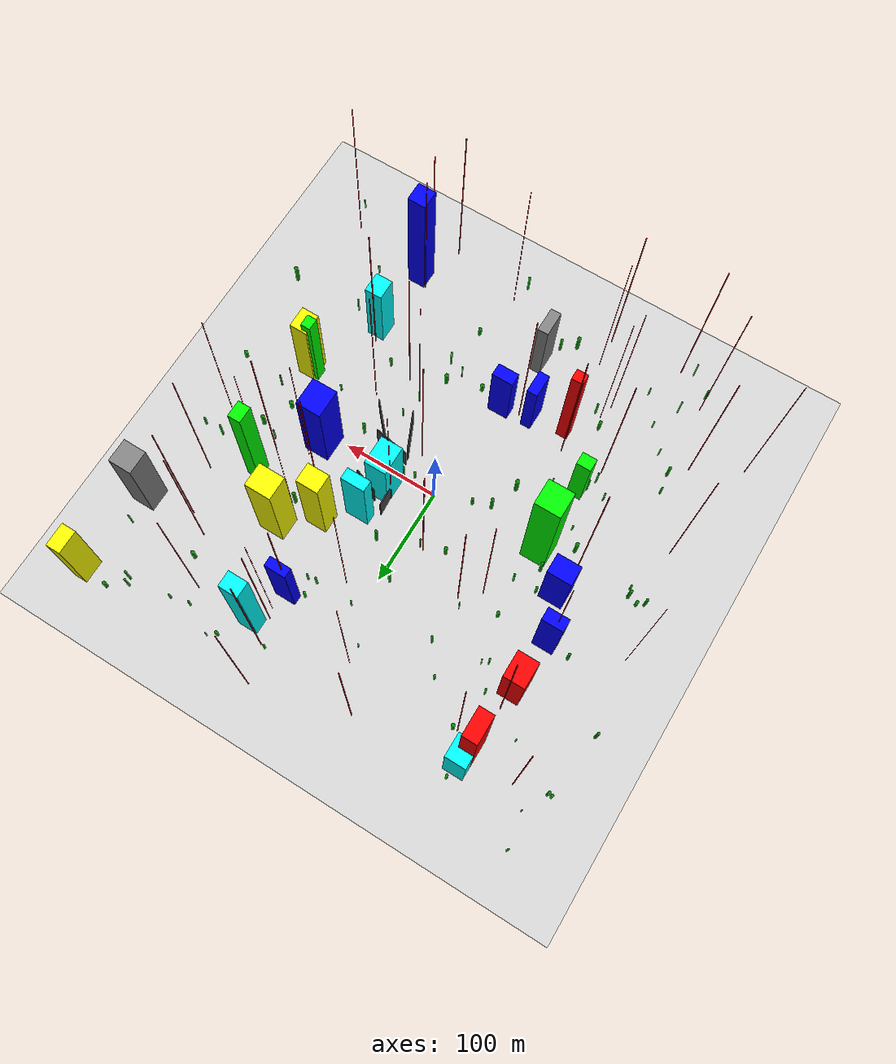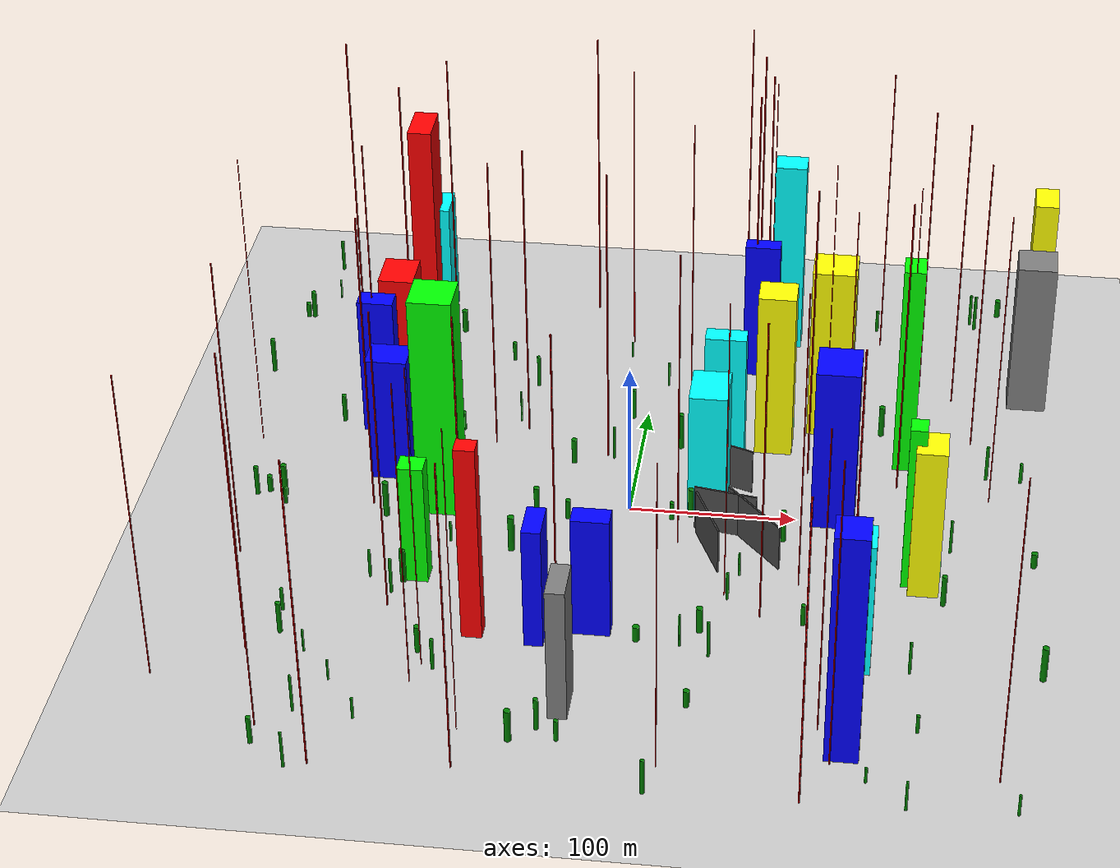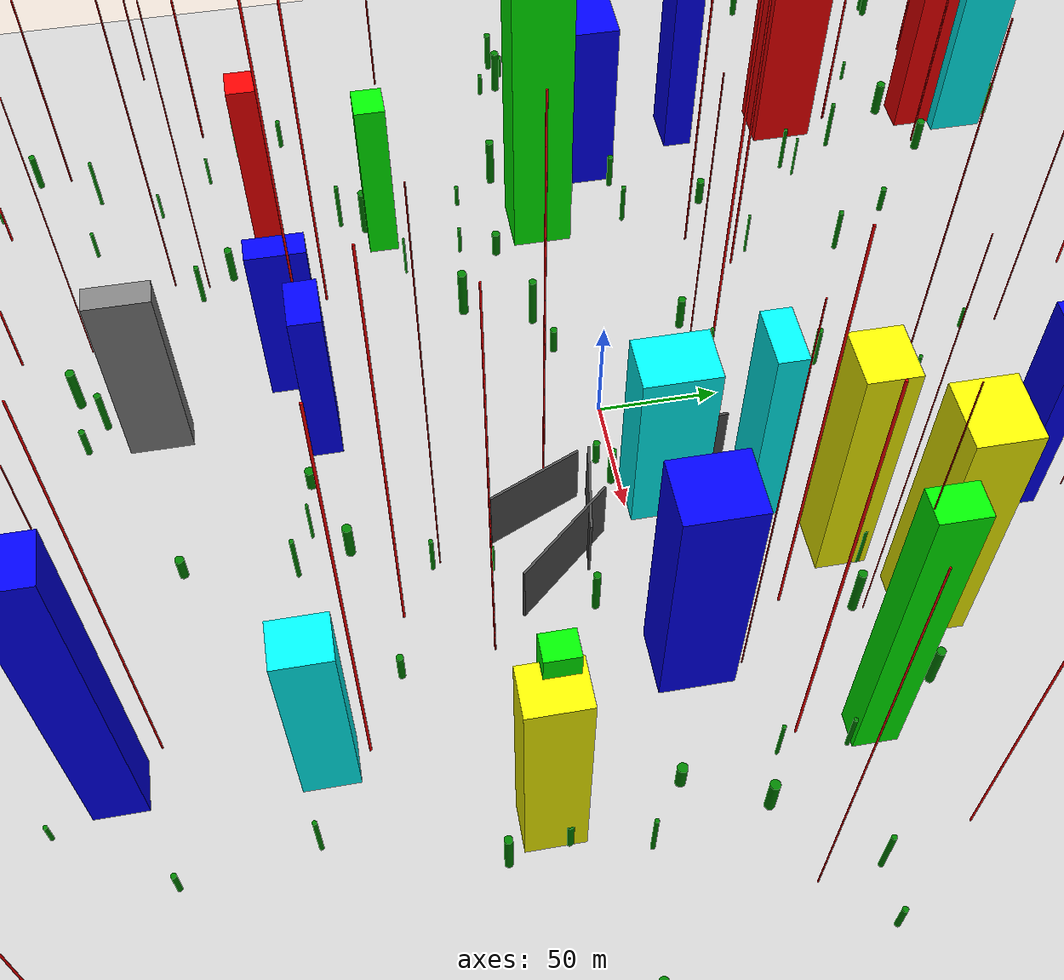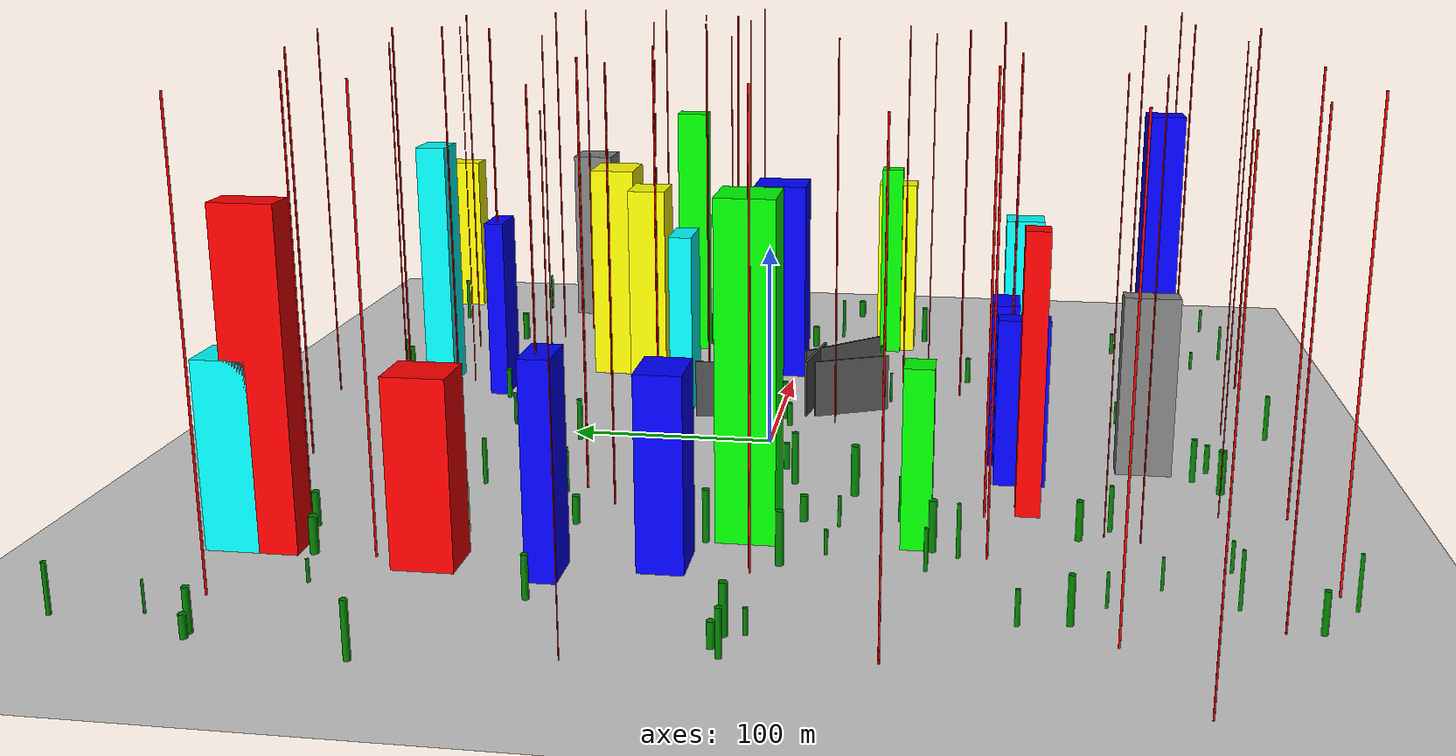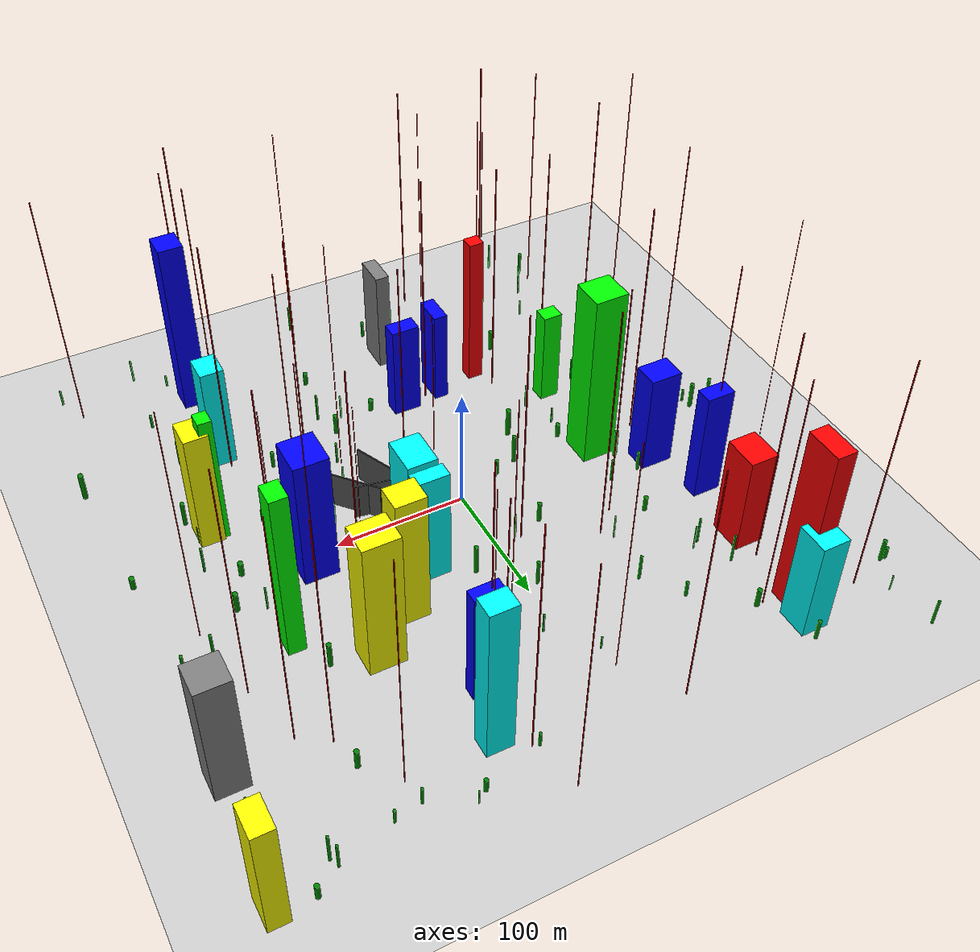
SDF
<sdf version="1.9">
 <world name="obstacles">
  <physics type="ode">
   <max_step_size>0.004</max_step_size>
   <real_time_factor>1.0</real_time_factor>
   <real_time_update_rate>250</real_time_update_rate>
  </physics>
  <spherical_coordinates>
   <surface_model>EARTH_WGS84</surface_model>
   <world_frame_orientation>ENU</world_frame_orientation>
   <latitude_deg>47.397971057728974</latitude_deg>
   <longitude_deg>8.546163739800146</longitude_deg>
   <elevation>0</elevation>
  </spherical_coordinates>
  <plugin name="gz::sim::systems::Physics" filename="gz-sim-physics-system"/>
  <plugin name="gz::sim::systems::UserCommands" filename="gz-sim-user-commands-system"/>
  <plugin name="gz::sim::systems::SceneBroadcaster" filename="gz-sim-scene-broadcaster-system"/>
  <plugin name="gz::sim::systems::Contact" filename="gz-sim-contact-system"/>
  <plugin name="gz::sim::systems::Imu" filename="gz-sim-imu-system"/>
  <plugin name="gz::sim::systems::AirPressure" filename="gz-sim-air-pressure-system"/>
  <plugin filename="gz-sim-air-speed-system" name="gz::sim::systems::AirSpeed"/>
  <plugin filename="gz-sim-apply-link-wrench-system" name="gz::sim::systems::ApplyLinkWrench"/>
  <plugin filename="gz-sim-navsat-system" name="gz::sim::systems::NavSat"/>
  <plugin filename="gz-sim-magnetometer-system" name="gz::sim::systems::Magnetometer"/>
  <plugin name="gz::sim::systems::Sensors" filename="gz-sim-sensors-system">
   <render_engine>ogre2</render_engine>
  </plugin>
  <scene>
   <ambient>1.0 1.0 1.0 1.0</ambient>
   <background>0.8 0.8 0.9 1.0</background>
   <grid>true</grid>
   <shadows>true</shadows>
  </scene>
  <light type="directional" name="sun">
   <pose>0 0 10 0 -0 0</pose>
   <diffuse>0.8 0.8 0.8 1</diffuse>
   <specular>0.2 0.2 0.2 1</specular>
   <attenuation>
    <range>1000</range>
    <constant>0.9</constant>
    <linear>0.01</linear>
    <quadratic>0.001</quadratic>
   </attenuation>
   <direction>-0.5 0.1 -0.9</direction>
  </light>
  <model name="ground_plane">
   <static>1</static>
   <link name="link">
    <collision name="collision">
     <geometry><plane><normal>0 0 1</normal><size>2000 2000</size></plane></geometry>
    </collision>
    <visual name="visual">
     <geometry><plane><normal>0 0 1</normal><size>2000 2000</size></plane></geometry>
     <material>
      <ambient>0.8 0.8 0.8 1</ambient>
      <diffuse>0.8 0.8 0.8 1</diffuse>
      <specular>0.8 0.8 0.8 1</specular>
     </material>
    </visual>
   </link>
  </model>
  <model name="Skyscraper_0">
   <pose>178 -54 50.5 0 0 0</pose>
   <static>1</static>
   <link name="link">
    <collision name="collision"><geometry><box><size>18 22 101</size></box></geometry></collision>
    <visual name="visual">
     <geometry><box><size>18 22 101</size></box></geometry>
     <material><ambient>1 1 0 1</ambient><diffuse>1 1 0 1</diffuse></material>
    </visual>
   </link>
  </model>
  <model name="Skyscraper_1">
   <pose>-165 70 47.0 0 0 0</pose>
   <static>1</static>
   <link name="link">
    <collision name="collision"><geometry><box><size>22 13 94</size></box></geometry></collision>
    <visual name="visual">
     <geometry><box><size>22 13 94</size></box></geometry>
     <material><ambient>0 0 1 1</ambient><diffuse>0 0 1 1</diffuse></material>
    </visual>
   </link>
  </model>
  <model name="Skyscraper_2">
   <pose>66 158 48.0 0 0 0</pose>
   <static>1</static>
   <link name="link">
    <collision name="collision"><geometry><box><size>22 10 96</size></box></geometry></collision>
    <visual name="visual">
     <geometry><box><size>22 10 96</size></box></geometry>
     <material><ambient>0 0 1 1</ambient><diffuse>0 0 1 1</diffuse></material>
    </visual>
   </link>
  </model>
  <model name="Skyscraper_3">
   <pose>244 237 48.0 0 0 0</pose>
   <static>1</static>
   <link name="link">
    <collision name="collision"><geometry><box><size>15 24 96</size></box></geometry></collision>
    <visual name="visual">
     <geometry><box><size>15 24 96</size></box></geometry>
     <material><ambient>1 1 0 1</ambient><diffuse>1 1 0 1</diffuse></material>
    </visual>
   </link>
  </model>
  <model name="Skyscraper_4">
   <pose>-17 -182 43.5 0 0 0</pose>
   <static>1</static>
   <link name="link">
    <collision name="collision"><geometry><box><size>11 26 87</size></box></geometry></collision>
    <visual name="visual">
     <geometry><box><size>11 26 87</size></box></geometry>
     <material><ambient>0.5 0.5 0.5 1</ambient><diffuse>0.5 0.5 0.5 1</diffuse></material>
    </visual>
   </link>
  </model>
  <model name="Skyscraper_5">
   <pose>-156 192 75.0 0 0 0</pose>
   <static>1</static>
   <link name="link">
    <collision name="collision"><geometry><box><size>15 28 150</size></box></geometry></collision>
    <visual name="visual">
     <geometry><box><size>15 28 150</size></box></geometry>
     <material><ambient>1 0 0 1</ambient><diffuse>1 0 0 1</diffuse></material>
    </visual>
   </link>
  </model>
  <model name="Skyscraper_6">
   <pose>-153 207 42.0 0 0 0</pose>
   <static>1</static>
   <link name="link">
    <collision name="collision"><geometry><box><size>21 24 84</size></box></geometry></collision>
    <visual name="visual">
     <geometry><box><size>21 24 84</size></box></geometry>
     <material><ambient>0 1 1 1</ambient><diffuse>0 1 1 1</diffuse></material>
    </visual>
   </link>
  </model>
  <model name="Skyscraper_7">
   <pose>-39 -123 40.0 0 0 0</pose>
   <static>1</static>
   <link name="link">
    <collision name="collision"><geometry><box><size>11 24 80</size></box></geometry></collision>
    <visual name="visual">
     <geometry><box><size>11 24 80</size></box></geometry>
     <material><ambient>0 0 1 1</ambient><diffuse>0 0 1 1</diffuse></material>
    </visual>
   </link>
  </model>
  <model name="Skyscraper_8">
   <pose>81 77 56.5 0 0 0</pose>
   <static>1</static>
   <link name="link">
    <collision name="collision"><geometry><box><size>23 20 113</size></box></geometry></collision>
    <visual name="visual">
     <geometry><box><size>23 20 113</size></box></geometry>
     <material><ambient>1 1 0 1</ambient><diffuse>1 1 0 1</diffuse></material>
    </visual>
   </link>
  </model>
  <model name="Skyscraper_9">
   <pose>139 -202 75.0 0 0 0</pose>
   <static>1</static>
   <link name="link">
    <collision name="collision"><geometry><box><size>19 20 150</size></box></geometry></collision>
    <visual name="visual">
     <geometry><box><size>19 20 150</size></box></geometry>
     <material><ambient>0 0 1 1</ambient><diffuse>0 0 1 1</diffuse></material>
    </visual>
   </link>
  </model>
  <model name="Skyscraper_10">
   <pose>114 103 59.0 0 0 0</pose>
   <static>1</static>
   <link name="link">
    <collision name="collision"><geometry><box><size>27 24 118</size></box></geometry></collision>
    <visual name="visual">
     <geometry><box><size>27 24 118</size></box></geometry>
     <material><ambient>1 1 0 1</ambient><diffuse>1 1 0 1</diffuse></material>
    </visual>
   </link>
  </model>
  <model name="Skyscraper_11">
   <pose>80 197 67.0 0 0 0</pose>
   <static>1</static>
   <link name="link">
    <collision name="collision"><geometry><box><size>20 16 134</size></box></geometry></collision>
    <visual name="visual">
     <geometry><box><size>20 16 134</size></box></geometry>
     <material><ambient>0 1 1 1</ambient><diffuse>0 1 1 1</diffuse></material>
    </visual>
   </link>
  </model>
  <model name="Skyscraper_12">
   <pose>52 53 47.5 0 0 0</pose>
   <static>1</static>
   <link name="link">
    <collision name="collision"><geometry><box><size>25 12 95</size></box></geometry></collision>
    <visual name="visual">
     <geometry><box><size>25 12 95</size></box></geometry>
     <material><ambient>0 1 1 1</ambient><diffuse>0 1 1 1</diffuse></material>
    </visual>
   </link>
  </model>
  <model name="Skyscraper_13">
   <pose>162 67 71.5 0 0 0</pose>
   <static>1</static>
   <link name="link">
    <collision name="collision"><geometry><box><size>13 17 143</size></box></geometry></collision>
    <visual name="visual">
     <geometry><box><size>13 17 143</size></box></geometry>
     <material><ambient>0 1 0 1</ambient><diffuse>0 1 0 1</diffuse></material>
    </visual>
   </link>
  </model>
  <model name="Skyscraper_14">
   <pose>-149 24 42.5 0 0 0</pose>
   <static>1</static>
   <link name="link">
    <collision name="collision"><geometry><box><size>25 20 85</size></box></geometry></collision>
    <visual name="visual">
     <geometry><box><size>25 20 85</size></box></geometry>
     <material><ambient>0 0 1 1</ambient><diffuse>0 0 1 1</diffuse></material>
    </visual>
   </link>
  </model>
  <model name="Skyscraper_15">
   <pose>-161 121 41.5 0 0 0</pose>
   <static>1</static>
   <link name="link">
    <collision name="collision"><geometry><box><size>22 27 83</size></box></geometry></collision>
    <visual name="visual">
     <geometry><box><size>22 27 83</size></box></geometry>
     <material><ambient>1 0 0 1</ambient><diffuse>1 0 0 1</diffuse></material>
    </visual>
   </link>
  </model>
  <model name="Skyscraper_16">
   <pose>170 -51 55.5 0 0 0</pose>
   <static>1</static>
   <link name="link">
    <collision name="collision"><geometry><box><size>10 12 111</size></box></geometry></collision>
    <visual name="visual">
     <geometry><box><size>10 12 111</size></box></geometry>
     <material><ambient>0 1 0 1</ambient><diffuse>0 1 0 1</diffuse></material>
    </visual>
   </link>
  </model>
  <model name="Skyscraper_17">
   <pose>142 -128 44.5 0 0 0</pose>
   <static>1</static>
   <link name="link">
    <collision name="collision"><geometry><box><size>18 21 89</size></box></geometry></collision>
    <visual name="visual">
     <geometry><box><size>18 21 89</size></box></geometry>
     <material><ambient>0 1 1 1</ambient><diffuse>0 1 1 1</diffuse></material>
    </visual>
   </link>
  </model>
  <model name="Skyscraper_18">
   <pose>-114 -6 75.0 0 0 0</pose>
   <static>1</static>
   <link name="link">
    <collision name="collision"><geometry><box><size>26 26 150</size></box></geometry></collision>
    <visual name="visual">
     <geometry><box><size>26 26 150</size></box></geometry>
     <material><ambient>0 1 0 1</ambient><diffuse>0 1 0 1</diffuse></material>
    </visual>
   </link>
  </model>
  <model name="Skyscraper_19">
   <pose>-75 -126 65.0 0 0 0</pose>
   <static>1</static>
   <link name="link">
    <collision name="collision"><geometry><box><size>12 11 130</size></box></geometry></collision>
    <visual name="visual">
     <geometry><box><size>12 11 130</size></box></geometry>
     <material><ambient>1 0 0 1</ambient><diffuse>1 0 0 1</diffuse></material>
    </visual>
   </link>
  </model>
  <model name="Skyscraper_20">
   <pose>122 9 55.0 0 0 0</pose>
   <static>1</static>
   <link name="link">
    <collision name="collision"><geometry><box><size>26 29 110</size></box></geometry></collision>
    <visual name="visual">
     <geometry><box><size>26 29 110</size></box></geometry>
     <material><ambient>0 0 1 1</ambient><diffuse>0 0 1 1</diffuse></material>
    </visual>
   </link>
  </model>
  <model name="Skyscraper_21">
   <pose>-116 -78 40.0 0 0 0</pose>
   <static>1</static>
   <link name="link">
    <collision name="collision"><geometry><box><size>15 13 80</size></box></geometry></collision>
    <visual name="visual">
     <geometry><box><size>15 13 80</size></box></geometry>
     <material><ambient>0 1 0 1</ambient><diffuse>0 1 0 1</diffuse></material>
    </visual>
   </link>
  </model>
  <model name="Skyscraper_22">
   <pose>46 16 41.5 0 0 0</pose>
   <static>1</static>
   <link name="link">
    <collision name="collision"><geometry><box><size>23 30 83</size></box></geometry></collision>
    <visual name="visual">
     <geometry><box><size>23 30 83</size></box></geometry>
     <material><ambient>0 1 1 1</ambient><diffuse>0 1 1 1</diffuse></material>
    </visual>
   </link>
  </model>
  <model name="Skyscraper_23">
   <pose>237 145 52.0 0 0 0</pose>
   <static>1</static>
   <link name="link">
    <collision name="collision"><geometry><box><size>24 24 104</size></box></geometry></collision>
    <visual name="visual">
     <geometry><box><size>24 24 104</size></box></geometry>
     <material><ambient>0.5 0.5 0.5 1</ambient><diffuse>0.5 0.5 0.5 1</diffuse></material>
    </visual>
   </link>
  </model>
  <model name="Skyscraper_24">
   <pose>-8 -115 40.0 0 0 0</pose>
   <static>1</static>
   <link name="link">
    <collision name="collision"><geometry><box><size>22 13 80</size></box></geometry></collision>
    <visual name="visual">
     <geometry><box><size>22 13 80</size></box></geometry>
     <material><ambient>0 0 1 1</ambient><diffuse>0 0 1 1</diffuse></material>
    </visual>
   </link>
  </model>
  <model name="Spire_0">
   <pose>169 151 100.0 0 0 0</pose>
   <static>1</static>
   <link name="link">
    <collision name="collision">
     <geometry><cylinder><radius>0.3851119192326981</radius><length>200</length></cylinder></geometry>
    </collision>
    <visual name="visual">
     <geometry><cylinder><radius>0.3851119192326981</radius><length>200</length></cylinder></geometry>
     <material><ambient>1 0 0 1</ambient><diffuse>1 0 0 1</diffuse></material>
    </visual>
   </link>
  </model>
  <model name="Spire_1">
   <pose>-204 198 100.0 0 0 0</pose>
   <static>1</static>
   <link name="link">
    <collision name="collision">
     <geometry><cylinder><radius>0.47903877447713844</radius><length>200</length></cylinder></geometry>
    </collision>
    <visual name="visual">
     <geometry><cylinder><radius>0.47903877447713844</radius><length>200</length></cylinder></geometry>
     <material><ambient>1 0 0 1</ambient><diffuse>1 0 0 1</diffuse></material>
    </visual>
   </link>
  </model>
  <model name="Spire_2">
   <pose>61 211 100.0 0 0 0</pose>
   <static>1</static>
   <link name="link">
    <collision name="collision">
     <geometry><cylinder><radius>0.4681673765856202</radius><length>200</length></cylinder></geometry>
    </collision>
    <visual name="visual">
     <geometry><cylinder><radius>0.4681673765856202</radius><length>200</length></cylinder></geometry>
     <material><ambient>1 0 0 1</ambient><diffuse>1 0 0 1</diffuse></material>
    </visual>
   </link>
  </model>
  <model name="Spire_3">
   <pose>-200 -156 100.0 0 0 0</pose>
   <static>1</static>
   <link name="link">
    <collision name="collision">
     <geometry><cylinder><radius>0.44581631200741345</radius><length>200</length></cylinder></geometry>
    </collision>
    <visual name="visual">
     <geometry><cylinder><radius>0.44581631200741345</radius><length>200</length></cylinder></geometry>
     <material><ambient>1 0 0 1</ambient><diffuse>1 0 0 1</diffuse></material>
    </visual>
   </link>
  </model>
  <model name="Spire_4">
   <pose>-224 -69 100.0 0 0 0</pose>
   <static>1</static>
   <link name="link">
    <collision name="collision">
     <geometry><cylinder><radius>0.3867186266921738</radius><length>200</length></cylinder></geometry>
    </collision>
    <visual name="visual">
     <geometry><cylinder><radius>0.3867186266921738</radius><length>200</length></cylinder></geometry>
     <material><ambient>1 0 0 1</ambient><diffuse>1 0 0 1</diffuse></material>
    </visual>
   </link>
  </model>
  <model name="Spire_5">
   <pose>62 158 100.0 0 0 0</pose>
   <static>1</static>
   <link name="link">
    <collision name="collision">
     <geometry><cylinder><radius>0.47709940659144723</radius><length>200</length></cylinder></geometry>
    </collision>
    <visual name="visual">
     <geometry><cylinder><radius>0.47709940659144723</radius><length>200</length></cylinder></geometry>
     <material><ambient>1 0 0 1</ambient><diffuse>1 0 0 1</diffuse></material>
    </visual>
   </link>
  </model>
  <model name="Spire_6">
   <pose>-47 222 100.0 0 0 0</pose>
   <static>1</static>
   <link name="link">
    <collision name="collision">
     <geometry><cylinder><radius>0.46595526813231736</radius><length>200</length></cylinder></geometry>
    </collision>
    <visual name="visual">
     <geometry><cylinder><radius>0.46595526813231736</radius><length>200</length></cylinder></geometry>
     <material><ambient>1 0 0 1</ambient><diffuse>1 0 0 1</diffuse></material>
    </visual>
   </link>
  </model>
  <model name="Spire_7">
   <pose>133 -214 100.0 0 0 0</pose>
   <static>1</static>
   <link name="link">
    <collision name="collision">
     <geometry><cylinder><radius>0.4003074017150695</radius><length>200</length></cylinder></geometry>
    </collision>
    <visual name="visual">
     <geometry><cylinder><radius>0.4003074017150695</radius><length>200</length></cylinder></geometry>
     <material><ambient>1 0 0 1</ambient><diffuse>1 0 0 1</diffuse></material>
    </visual>
   </link>
  </model>
  <model name="Spire_8">
   <pose>128 28 100.0 0 0 0</pose>
   <static>1</static>
   <link name="link">
    <collision name="collision">
     <geometry><cylinder><radius>0.264902842425644</radius><length>200</length></cylinder></geometry>
    </collision>
    <visual name="visual">
     <geometry><cylinder><radius>0.264902842425644</radius><length>200</length></cylinder></geometry>
     <material><ambient>1 0 0 1</ambient><diffuse>1 0 0 1</diffuse></material>
    </visual>
   </link>
  </model>
  <model name="Spire_9">
   <pose>159 40 100.0 0 0 0</pose>
   <static>1</static>
   <link name="link">
    <collision name="collision">
     <geometry><cylinder><radius>0.47379488322787233</radius><length>200</length></cylinder></geometry>
    </collision>
    <visual name="visual">
     <geometry><cylinder><radius>0.47379488322787233</radius><length>200</length></cylinder></geometry>
     <material><ambient>1 0 0 1</ambient><diffuse>1 0 0 1</diffuse></material>
    </visual>
   </link>
  </model>
  <model name="Spire_10">
   <pose>106 -62 100.0 0 0 0</pose>
   <static>1</static>
   <link name="link">
    <collision name="collision">
     <geometry><cylinder><radius>0.33962730395507773</radius><length>200</length></cylinder></geometry>
    </collision>
    <visual name="visual">
     <geometry><cylinder><radius>0.33962730395507773</radius><length>200</length></cylinder></geometry>
     <material><ambient>1 0 0 1</ambient><diffuse>1 0 0 1</diffuse></material>
    </visual>
   </link>
  </model>
  <model name="Spire_11">
   <pose>-20 53 100.0 0 0 0</pose>
   <static>1</static>
   <link name="link">
    <collision name="collision">
     <geometry><cylinder><radius>0.491058295464967</radius><length>200</length></cylinder></geometry>
    </collision>
    <visual name="visual">
     <geometry><cylinder><radius>0.491058295464967</radius><length>200</length></cylinder></geometry>
     <material><ambient>1 0 0 1</ambient><diffuse>1 0 0 1</diffuse></material>
    </visual>
   </link>
  </model>
  <model name="Spire_12">
   <pose>-168 71 100.0 0 0 0</pose>
   <static>1</static>
   <link name="link">
    <collision name="collision">
     <geometry><cylinder><radius>0.3735198801167253</radius><length>200</length></cylinder></geometry>
    </collision>
    <visual name="visual">
     <geometry><cylinder><radius>0.3735198801167253</radius><length>200</length></cylinder></geometry>
     <material><ambient>1 0 0 1</ambient><diffuse>1 0 0 1</diffuse></material>
    </visual>
   </link>
  </model>
  <model name="Spire_13">
   <pose>25 119 100.0 0 0 0</pose>
   <static>1</static>
   <link name="link">
    <collision name="collision">
     <geometry><cylinder><radius>0.2927591307399839</radius><length>200</length></cylinder></geometry>
    </collision>
    <visual name="visual">
     <geometry><cylinder><radius>0.2927591307399839</radius><length>200</length></cylinder></geometry>
     <material><ambient>1 0 0 1</ambient><diffuse>1 0 0 1</diffuse></material>
    </visual>
   </link>
  </model>
  <model name="Spire_14">
   <pose>-28 -118 100.0 0 0 0</pose>
   <static>1</static>
   <link name="link">
    <collision name="collision">
     <geometry><cylinder><radius>0.45911367101460715</radius><length>200</length></cylinder></geometry>
    </collision>
    <visual name="visual">
     <geometry><cylinder><radius>0.45911367101460715</radius><length>200</length></cylinder></geometry>
     <material><ambient>1 0 0 1</ambient><diffuse>1 0 0 1</diffuse></material>
    </visual>
   </link>
  </model>
  <model name="Spire_15">
   <pose>-70 -210 100.0 0 0 0</pose>
   <static>1</static>
   <link name="link">
    <collision name="collision">
     <geometry><cylinder><radius>0.21747525304132187</radius><length>200</length></cylinder></geometry>
    </collision>
    <visual name="visual">
     <geometry><cylinder><radius>0.21747525304132187</radius><length>200</length></cylinder></geometry>
     <material><ambient>1 0 0 1</ambient><diffuse>1 0 0 1</diffuse></material>
    </visual>
   </link>
  </model>
  <model name="Spire_16">
   <pose>-83 -107 100.0 0 0 0</pose>
   <static>1</static>
   <link name="link">
    <collision name="collision">
     <geometry><cylinder><radius>0.4890352460882555</radius><length>200</length></cylinder></geometry>
    </collision>
    <visual name="visual">
     <geometry><cylinder><radius>0.4890352460882555</radius><length>200</length></cylinder></geometry>
     <material><ambient>1 0 0 1</ambient><diffuse>1 0 0 1</diffuse></material>
    </visual>
   </link>
  </model>
  <model name="Spire_17">
   <pose>-145 -246 100.0 0 0 0</pose>
   <static>1</static>
   <link name="link">
    <collision name="collision">
     <geometry><cylinder><radius>0.47034292058402727</radius><length>200</length></cylinder></geometry>
    </collision>
    <visual name="visual">
     <geometry><cylinder><radius>0.47034292058402727</radius><length>200</length></cylinder></geometry>
     <material><ambient>1 0 0 1</ambient><diffuse>1 0 0 1</diffuse></material>
    </visual>
   </link>
  </model>
  <model name="Spire_18">
   <pose>71 177 100.0 0 0 0</pose>
   <static>1</static>
   <link name="link">
    <collision name="collision">
     <geometry><cylinder><radius>0.21156406738607572</radius><length>200</length></cylinder></geometry>
    </collision>
    <visual name="visual">
     <geometry><cylinder><radius>0.21156406738607572</radius><length>200</length></cylinder></geometry>
     <material><ambient>1 0 0 1</ambient><diffuse>1 0 0 1</diffuse></material>
    </visual>
   </link>
  </model>
  <model name="Spire_19">
   <pose>-128 -108 100.0 0 0 0</pose>
   <static>1</static>
   <link name="link">
    <collision name="collision">
     <geometry><cylinder><radius>0.45270289470616354</radius><length>200</length></cylinder></geometry>
    </collision>
    <visual name="visual">
     <geometry><cylinder><radius>0.45270289470616354</radius><length>200</length></cylinder></geometry>
     <material><ambient>1 0 0 1</ambient><diffuse>1 0 0 1</diffuse></material>
    </visual>
   </link>
  </model>
  <model name="Spire_20">
   <pose>-248 -183 100.0 0 0 0</pose>
   <static>1</static>
   <link name="link">
    <collision name="collision">
     <geometry><cylinder><radius>0.34875254827759905</radius><length>200</length></cylinder></geometry>
    </collision>
    <visual name="visual">
     <geometry><cylinder><radius>0.34875254827759905</radius><length>200</length></cylinder></geometry>
     <material><ambient>1 0 0 1</ambient><diffuse>1 0 0 1</diffuse></material>
    </visual>
   </link>
  </model>
  <model name="Spire_21">
   <pose>139 -113 100.0 0 0 0</pose>
   <static>1</static>
   <link name="link">
    <collision name="collision">
     <geometry><cylinder><radius>0.48218072428795306</radius><length>200</length></cylinder></geometry>
    </collision>
    <visual name="visual">
     <geometry><cylinder><radius>0.48218072428795306</radius><length>200</length></cylinder></geometry>
     <material><ambient>1 0 0 1</ambient><diffuse>1 0 0 1</diffuse></material>
    </visual>
   </link>
  </model>
  <model name="Spire_22">
   <pose>-237 46 100.0 0 0 0</pose>
   <static>1</static>
   <link name="link">
    <collision name="collision">
     <geometry><cylinder><radius>0.20411459557960163</radius><length>200</length></cylinder></geometry>
    </collision>
    <visual name="visual">
     <geometry><cylinder><radius>0.20411459557960163</radius><length>200</length></cylinder></geometry>
     <material><ambient>1 0 0 1</ambient><diffuse>1 0 0 1</diffuse></material>
    </visual>
   </link>
  </model>
  <model name="Spire_23">
   <pose>-155 -12 100.0 0 0 0</pose>
   <static>1</static>
   <link name="link">
    <collision name="collision">
     <geometry><cylinder><radius>0.4816834138203816</radius><length>200</length></cylinder></geometry>
    </collision>
    <visual name="visual">
     <geometry><cylinder><radius>0.4816834138203816</radius><length>200</length></cylinder></geometry>
     <material><ambient>1 0 0 1</ambient><diffuse>1 0 0 1</diffuse></material>
    </visual>
   </link>
  </model>
  <model name="Spire_24">
   <pose>86 -94 100.0 0 0 0</pose>
   <static>1</static>
   <link name="link">
    <collision name="collision">
     <geometry><cylinder><radius>0.4521577670168428</radius><length>200</length></cylinder></geometry>
    </collision>
    <visual name="visual">
     <geometry><cylinder><radius>0.4521577670168428</radius><length>200</length></cylinder></geometry>
     <material><ambient>1 0 0 1</ambient><diffuse>1 0 0 1</diffuse></material>
    </visual>
   </link>
  </model>
  <model name="Spire_25">
   <pose>163 59 100.0 0 0 0</pose>
   <static>1</static>
   <link name="link">
    <collision name="collision">
     <geometry><cylinder><radius>0.21299335867764213</radius><length>200</length></cylinder></geometry>
    </collision>
    <visual name="visual">
     <geometry><cylinder><radius>0.21299335867764213</radius><length>200</length></cylinder></geometry>
     <material><ambient>1 0 0 1</ambient><diffuse>1 0 0 1</diffuse></material>
    </visual>
   </link>
  </model>
  <model name="Spire_26">
   <pose>68 186 100.0 0 0 0</pose>
   <static>1</static>
   <link name="link">
    <collision name="collision">
     <geometry><cylinder><radius>0.40675459533983915</radius><length>200</length></cylinder></geometry>
    </collision>
    <visual name="visual">
     <geometry><cylinder><radius>0.40675459533983915</radius><length>200</length></cylinder></geometry>
     <material><ambient>1 0 0 1</ambient><diffuse>1 0 0 1</diffuse></material>
    </visual>
   </link>
  </model>
  <model name="Spire_27">
   <pose>-19 182 100.0 0 0 0</pose>
   <static>1</static>
   <link name="link">
    <collision name="collision">
     <geometry><cylinder><radius>0.28773696133445054</radius><length>200</length></cylinder></geometry>
    </collision>
    <visual name="visual">
     <geometry><cylinder><radius>0.28773696133445054</radius><length>200</length></cylinder></geometry>
     <material><ambient>1 0 0 1</ambient><diffuse>1 0 0 1</diffuse></material>
    </visual>
   </link>
  </model>
  <model name="Spire_28">
   <pose>104 49 100.0 0 0 0</pose>
   <static>1</static>
   <link name="link">
    <collision name="collision">
     <geometry><cylinder><radius>0.473827415521029</radius><length>200</length></cylinder></geometry>
    </collision>
    <visual name="visual">
     <geometry><cylinder><radius>0.473827415521029</radius><length>200</length></cylinder></geometry>
     <material><ambient>1 0 0 1</ambient><diffuse>1 0 0 1</diffuse></material>
    </visual>
   </link>
  </model>
  <model name="Spire_29">
   <pose>-73 76 100.0 0 0 0</pose>
   <static>1</static>
   <link name="link">
    <collision name="collision">
     <geometry><cylinder><radius>0.46499906401050634</radius><length>200</length></cylinder></geometry>
    </collision>
    <visual name="visual">
     <geometry><cylinder><radius>0.46499906401050634</radius><length>200</length></cylinder></geometry>
     <material><ambient>1 0 0 1</ambient><diffuse>1 0 0 1</diffuse></material>
    </visual>
   </link>
  </model>
  <model name="Spire_30">
   <pose>-103 -173 100.0 0 0 0</pose>
   <static>1</static>
   <link name="link">
    <collision name="collision">
     <geometry><cylinder><radius>0.29753795313489706</radius><length>200</length></cylinder></geometry>
    </collision>
    <visual name="visual">
     <geometry><cylinder><radius>0.29753795313489706</radius><length>200</length></cylinder></geometry>
     <material><ambient>1 0 0 1</ambient><diffuse>1 0 0 1</diffuse></material>
    </visual>
   </link>
  </model>
  <model name="Spire_31">
   <pose>-91 59 100.0 0 0 0</pose>
   <static>1</static>
   <link name="link">
    <collision name="collision">
     <geometry><cylinder><radius>0.4091152607712939</radius><length>200</length></cylinder></geometry>
    </collision>
    <visual name="visual">
     <geometry><cylinder><radius>0.4091152607712939</radius><length>200</length></cylinder></geometry>
     <material><ambient>1 0 0 1</ambient><diffuse>1 0 0 1</diffuse></material>
    </visual>
   </link>
  </model>
  <model name="Spire_32">
   <pose>224 -218 100.0 0 0 0</pose>
   <static>1</static>
   <link name="link">
    <collision name="collision">
     <geometry><cylinder><radius>0.3545172343501649</radius><length>200</length></cylinder></geometry>
    </collision>
    <visual name="visual">
     <geometry><cylinder><radius>0.3545172343501649</radius><length>200</length></cylinder></geometry>
     <material><ambient>1 0 0 1</ambient><diffuse>1 0 0 1</diffuse></material>
    </visual>
   </link>
  </model>
  <model name="Spire_33">
   <pose>-180 -219 100.0 0 0 0</pose>
   <static>1</static>
   <link name="link">
    <collision name="collision">
     <geometry><cylinder><radius>0.3727092924935774</radius><length>200</length></cylinder></geometry>
    </collision>
    <visual name="visual">
     <geometry><cylinder><radius>0.3727092924935774</radius><length>200</length></cylinder></geometry>
     <material><ambient>1 0 0 1</ambient><diffuse>1 0 0 1</diffuse></material>
    </visual>
   </link>
  </model>
  <model name="Spire_34">
   <pose>215 32 100.0 0 0 0</pose>
   <static>1</static>
   <link name="link">
    <collision name="collision">
     <geometry><cylinder><radius>0.2875692238965125</radius><length>200</length></cylinder></geometry>
    </collision>
    <visual name="visual">
     <geometry><cylinder><radius>0.2875692238965125</radius><length>200</length></cylinder></geometry>
     <material><ambient>1 0 0 1</ambient><diffuse>1 0 0 1</diffuse></material>
    </visual>
   </link>
  </model>
  <model name="Spire_35">
   <pose>-160 145 100.0 0 0 0</pose>
   <static>1</static>
   <link name="link">
    <collision name="collision">
     <geometry><cylinder><radius>0.49343203120130574</radius><length>200</length></cylinder></geometry>
    </collision>
    <visual name="visual">
     <geometry><cylinder><radius>0.49343203120130574</radius><length>200</length></cylinder></geometry>
     <material><ambient>1 0 0 1</ambient><diffuse>1 0 0 1</diffuse></material>
    </visual>
   </link>
  </model>
  <model name="Spire_36">
   <pose>-68 -240 100.0 0 0 0</pose>
   <static>1</static>
   <link name="link">
    <collision name="collision">
     <geometry><cylinder><radius>0.4473573558580615</radius><length>200</length></cylinder></geometry>
    </collision>
    <visual name="visual">
     <geometry><cylinder><radius>0.4473573558580615</radius><length>200</length></cylinder></geometry>
     <material><ambient>1 0 0 1</ambient><diffuse>1 0 0 1</diffuse></material>
    </visual>
   </link>
  </model>
  <model name="Spire_37">
   <pose>142 197 100.0 0 0 0</pose>
   <static>1</static>
   <link name="link">
    <collision name="collision">
     <geometry><cylinder><radius>0.33149318535785816</radius><length>200</length></cylinder></geometry>
    </collision>
    <visual name="visual">
     <geometry><cylinder><radius>0.33149318535785816</radius><length>200</length></cylinder></geometry>
     <material><ambient>1 0 0 1</ambient><diffuse>1 0 0 1</diffuse></material>
    </visual>
   </link>
  </model>
  <model name="Spire_38">
   <pose>50 248 100.0 0 0 0</pose>
   <static>1</static>
   <link name="link">
    <collision name="collision">
     <geometry><cylinder><radius>0.3699464935165014</radius><length>200</length></cylinder></geometry>
    </collision>
    <visual name="visual">
     <geometry><cylinder><radius>0.3699464935165014</radius><length>200</length></cylinder></geometry>
     <material><ambient>1 0 0 1</ambient><diffuse>1 0 0 1</diffuse></material>
    </visual>
   </link>
  </model>
  <model name="Spire_39">
   <pose>113 80 100.0 0 0 0</pose>
   <static>1</static>
   <link name="link">
    <collision name="collision">
     <geometry><cylinder><radius>0.20116611847402452</radius><length>200</length></cylinder></geometry>
    </collision>
    <visual name="visual">
     <geometry><cylinder><radius>0.20116611847402452</radius><length>200</length></cylinder></geometry>
     <material><ambient>1 0 0 1</ambient><diffuse>1 0 0 1</diffuse></material>
    </visual>
   </link>
  </model>
  <model name="Spire_40">
   <pose>190 138 100.0 0 0 0</pose>
   <static>1</static>
   <link name="link">
    <collision name="collision">
     <geometry><cylinder><radius>0.3767838128567847</radius><length>200</length></cylinder></geometry>
    </collision>
    <visual name="visual">
     <geometry><cylinder><radius>0.3767838128567847</radius><length>200</length></cylinder></geometry>
     <material><ambient>1 0 0 1</ambient><diffuse>1 0 0 1</diffuse></material>
    </visual>
   </link>
  </model>
  <model name="Spire_41">
   <pose>64 -77 100.0 0 0 0</pose>
   <static>1</static>
   <link name="link">
    <collision name="collision">
     <geometry><cylinder><radius>0.24775819546895705</radius><length>200</length></cylinder></geometry>
    </collision>
    <visual name="visual">
     <geometry><cylinder><radius>0.24775819546895705</radius><length>200</length></cylinder></geometry>
     <material><ambient>1 0 0 1</ambient><diffuse>1 0 0 1</diffuse></material>
    </visual>
   </link>
  </model>
  <model name="Spire_42">
   <pose>119 -246 100.0 0 0 0</pose>
   <static>1</static>
   <link name="link">
    <collision name="collision">
     <geometry><cylinder><radius>0.46672014287727004</radius><length>200</length></cylinder></geometry>
    </collision>
    <visual name="visual">
     <geometry><cylinder><radius>0.46672014287727004</radius><length>200</length></cylinder></geometry>
     <material><ambient>1 0 0 1</ambient><diffuse>1 0 0 1</diffuse></material>
    </visual>
   </link>
  </model>
  <model name="Spire_43">
   <pose>32 -30 100.0 0 0 0</pose>
   <static>1</static>
   <link name="link">
    <collision name="collision">
     <geometry><cylinder><radius>0.382958132884067</radius><length>200</length></cylinder></geometry>
    </collision>
    <visual name="visual">
     <geometry><cylinder><radius>0.382958132884067</radius><length>200</length></cylinder></geometry>
     <material><ambient>1 0 0 1</ambient><diffuse>1 0 0 1</diffuse></material>
    </visual>
   </link>
  </model>
  <model name="Spire_44">
   <pose>-137 183 100.0 0 0 0</pose>
   <static>1</static>
   <link name="link">
    <collision name="collision">
     <geometry><cylinder><radius>0.412006816319749</radius><length>200</length></cylinder></geometry>
    </collision>
    <visual name="visual">
     <geometry><cylinder><radius>0.412006816319749</radius><length>200</length></cylinder></geometry>
     <material><ambient>1 0 0 1</ambient><diffuse>1 0 0 1</diffuse></material>
    </visual>
   </link>
  </model>
  <model name="Spire_45">
   <pose>-99 -158 100.0 0 0 0</pose>
   <static>1</static>
   <link name="link">
    <collision name="collision">
     <geometry><cylinder><radius>0.24139794060250905</radius><length>200</length></cylinder></geometry>
    </collision>
    <visual name="visual">
     <geometry><cylinder><radius>0.24139794060250905</radius><length>200</length></cylinder></geometry>
     <material><ambient>1 0 0 1</ambient><diffuse>1 0 0 1</diffuse></material>
    </visual>
   </link>
  </model>
  <model name="Spire_46">
   <pose>125 -187 100.0 0 0 0</pose>
   <static>1</static>
   <link name="link">
    <collision name="collision">
     <geometry><cylinder><radius>0.3491397350114776</radius><length>200</length></cylinder></geometry>
    </collision>
    <visual name="visual">
     <geometry><cylinder><radius>0.3491397350114776</radius><length>200</length></cylinder></geometry>
     <material><ambient>1 0 0 1</ambient><diffuse>1 0 0 1</diffuse></material>
    </visual>
   </link>
  </model>
  <model name="Spire_47">
   <pose>34 24 100.0 0 0 0</pose>
   <static>1</static>
   <link name="link">
    <collision name="collision">
     <geometry><cylinder><radius>0.2411957361269375</radius><length>200</length></cylinder></geometry>
    </collision>
    <visual name="visual">
     <geometry><cylinder><radius>0.2411957361269375</radius><length>200</length></cylinder></geometry>
     <material><ambient>1 0 0 1</ambient><diffuse>1 0 0 1</diffuse></material>
    </visual>
   </link>
  </model>
  <model name="Spire_48">
   <pose>203 91 100.0 0 0 0</pose>
   <static>1</static>
   <link name="link">
    <collision name="collision">
     <geometry><cylinder><radius>0.3654331721300669</radius><length>200</length></cylinder></geometry>
    </collision>
    <visual name="visual">
     <geometry><cylinder><radius>0.3654331721300669</radius><length>200</length></cylinder></geometry>
     <material><ambient>1 0 0 1</ambient><diffuse>1 0 0 1</diffuse></material>
    </visual>
   </link>
  </model>
  <model name="Spire_49">
   <pose>41 -227 100.0 0 0 0</pose>
   <static>1</static>
   <link name="link">
    <collision name="collision">
     <geometry><cylinder><radius>0.26238059529766616</radius><length>200</length></cylinder></geometry>
    </collision>
    <visual name="visual">
     <geometry><cylinder><radius>0.26238059529766616</radius><length>200</length></cylinder></geometry>
     <material><ambient>1 0 0 1</ambient><diffuse>1 0 0 1</diffuse></material>
    </visual>
   </link>
  </model>
  <model name="Tree_0">
   <pose>234 -242 7.0 0 0 0</pose>
   <static>1</static>
   <link name="link">
    <collision name="collision">
     <geometry><cylinder><radius>0.7775662024568268</radius><length>14</length></cylinder></geometry>
    </collision>
    <visual name="visual">
     <geometry><cylinder><radius>0.7775662024568268</radius><length>14</length></cylinder></geometry>
     <material><ambient>0 0.5 0 1</ambient><diffuse>0 0.5 0 1</diffuse></material>
    </visual>
   </link>
  </model>
  <model name="Tree_1">
   <pose>-162 -205 12.5 0 0 0</pose>
   <static>1</static>
   <link name="link">
    <collision name="collision">
     <geometry><cylinder><radius>0.7847532740561793</radius><length>25</length></cylinder></geometry>
    </collision>
    <visual name="visual">
     <geometry><cylinder><radius>0.7847532740561793</radius><length>25</length></cylinder></geometry>
     <material><ambient>0 0.5 0 1</ambient><diffuse>0 0.5 0 1</diffuse></material>
    </visual>
   </link>
  </model>
  <model name="Tree_2">
   <pose>18 -123 5.0 0 0 0</pose>
   <static>1</static>
   <link name="link">
    <collision name="collision">
     <geometry><cylinder><radius>1.9860177778806496</radius><length>10</length></cylinder></geometry>
    </collision>
    <visual name="visual">
     <geometry><cylinder><radius>1.9860177778806496</radius><length>10</length></cylinder></geometry>
     <material><ambient>0 0.5 0 1</ambient><diffuse>0 0.5 0 1</diffuse></material>
    </visual>
   </link>
  </model>
  <model name="Tree_3">
   <pose>-148 -177 7.0 0 0 0</pose>
   <static>1</static>
   <link name="link">
    <collision name="collision">
     <geometry><cylinder><radius>0.6288832305850341</radius><length>14</length></cylinder></geometry>
    </collision>
    <visual name="visual">
     <geometry><cylinder><radius>0.6288832305850341</radius><length>14</length></cylinder></geometry>
     <material><ambient>0 0.5 0 1</ambient><diffuse>0 0.5 0 1</diffuse></material>
    </visual>
   </link>
  </model>
  <model name="Tree_4">
   <pose>94 -21 11.0 0 0 0</pose>
   <static>1</static>
   <link name="link">
    <collision name="collision">
     <geometry><cylinder><radius>1.4907200034802457</radius><length>22</length></cylinder></geometry>
    </collision>
    <visual name="visual">
     <geometry><cylinder><radius>1.4907200034802457</radius><length>22</length></cylinder></geometry>
     <material><ambient>0 0.5 0 1</ambient><diffuse>0 0.5 0 1</diffuse></material>
    </visual>
   </link>
  </model>
  <model name="Tree_5">
   <pose>139 215 7.5 0 0 0</pose>
   <static>1</static>
   <link name="link">
    <collision name="collision">
     <geometry><cylinder><radius>0.992268738689231</radius><length>15</length></cylinder></geometry>
    </collision>
    <visual name="visual">
     <geometry><cylinder><radius>0.992268738689231</radius><length>15</length></cylinder></geometry>
     <material><ambient>0 0.5 0 1</ambient><diffuse>0 0.5 0 1</diffuse></material>
    </visual>
   </link>
  </model>
  <model name="Tree_6">
   <pose>43 -125 11.0 0 0 0</pose>
   <static>1</static>
   <link name="link">
    <collision name="collision">
     <geometry><cylinder><radius>0.6350662108455527</radius><length>22</length></cylinder></geometry>
    </collision>
    <visual name="visual">
     <geometry><cylinder><radius>0.6350662108455527</radius><length>22</length></cylinder></geometry>
     <material><ambient>0 0.5 0 1</ambient><diffuse>0 0.5 0 1</diffuse></material>
    </visual>
   </link>
  </model>
  <model name="Tree_7">
   <pose>213 55 12.0 0 0 0</pose>
   <static>1</static>
   <link name="link">
    <collision name="collision">
     <geometry><cylinder><radius>1.0092724083176572</radius><length>24</length></cylinder></geometry>
    </collision>
    <visual name="visual">
     <geometry><cylinder><radius>1.0092724083176572</radius><length>24</length></cylinder></geometry>
     <material><ambient>0 0.5 0 1</ambient><diffuse>0 0.5 0 1</diffuse></material>
    </visual>
   </link>
  </model>
  <model name="Tree_8">
   <pose>-109 33 10.0 0 0 0</pose>
   <static>1</static>
   <link name="link">
    <collision name="collision">
     <geometry><cylinder><radius>1.0057800512753245</radius><length>20</length></cylinder></geometry>
    </collision>
    <visual name="visual">
     <geometry><cylinder><radius>1.0057800512753245</radius><length>20</length></cylinder></geometry>
     <material><ambient>0 0.5 0 1</ambient><diffuse>0 0.5 0 1</diffuse></material>
    </visual>
   </link>
  </model>
  <model name="Tree_9">
   <pose>49 134 9.0 0 0 0</pose>
   <static>1</static>
   <link name="link">
    <collision name="collision">
     <geometry><cylinder><radius>1.1132183289719126</radius><length>18</length></cylinder></geometry>
    </collision>
    <visual name="visual">
     <geometry><cylinder><radius>1.1132183289719126</radius><length>18</length></cylinder></geometry>
     <material><ambient>0 0.5 0 1</ambient><diffuse>0 0.5 0 1</diffuse></material>
    </visual>
   </link>
  </model>
  <model name="Tree_10">
   <pose>109 231 6.5 0 0 0</pose>
   <static>1</static>
   <link name="link">
    <collision name="collision">
     <geometry><cylinder><radius>0.5402390580962825</radius><length>13</length></cylinder></geometry>
    </collision>
    <visual name="visual">
     <geometry><cylinder><radius>0.5402390580962825</radius><length>13</length></cylinder></geometry>
     <material><ambient>0 0.5 0 1</ambient><diffuse>0 0.5 0 1</diffuse></material>
    </visual>
   </link>
  </model>
  <model name="Tree_11">
   <pose>101 225 5.5 0 0 0</pose>
   <static>1</static>
   <link name="link">
    <collision name="collision">
     <geometry><cylinder><radius>1.529085495039706</radius><length>11</length></cylinder></geometry>
    </collision>
    <visual name="visual">
     <geometry><cylinder><radius>1.529085495039706</radius><length>11</length></cylinder></geometry>
     <material><ambient>0 0.5 0 1</ambient><diffuse>0 0.5 0 1</diffuse></material>
    </visual>
   </link>
  </model>
  <model name="Tree_12">
   <pose>56 212 6.0 0 0 0</pose>
   <static>1</static>
   <link name="link">
    <collision name="collision">
     <geometry><cylinder><radius>1.0685253667157792</radius><length>12</length></cylinder></geometry>
    </collision>
    <visual name="visual">
     <geometry><cylinder><radius>1.0685253667157792</radius><length>12</length></cylinder></geometry>
     <material><ambient>0 0.5 0 1</ambient><diffuse>0 0.5 0 1</diffuse></material>
    </visual>
   </link>
  </model>
  <model name="Tree_13">
   <pose>200 230 11.0 0 0 0</pose>
   <static>1</static>
   <link name="link">
    <collision name="collision">
     <geometry><cylinder><radius>0.9260853299380698</radius><length>22</length></cylinder></geometry>
    </collision>
    <visual name="visual">
     <geometry><cylinder><radius>0.9260853299380698</radius><length>22</length></cylinder></geometry>
     <material><ambient>0 0.5 0 1</ambient><diffuse>0 0.5 0 1</diffuse></material>
    </visual>
   </link>
  </model>
  <model name="Tree_14">
   <pose>71 -57 8.0 0 0 0</pose>
   <static>1</static>
   <link name="link">
    <collision name="collision">
     <geometry><cylinder><radius>0.6698129040329539</radius><length>16</length></cylinder></geometry>
    </collision>
    <visual name="visual">
     <geometry><cylinder><radius>0.6698129040329539</radius><length>16</length></cylinder></geometry>
     <material><ambient>0 0.5 0 1</ambient><diffuse>0 0.5 0 1</diffuse></material>
    </visual>
   </link>
  </model>
  <model name="Tree_15">
   <pose>-114 71 6.5 0 0 0</pose>
   <static>1</static>
   <link name="link">
    <collision name="collision">
     <geometry><cylinder><radius>1.70457057995222</radius><length>13</length></cylinder></geometry>
    </collision>
    <visual name="visual">
     <geometry><cylinder><radius>1.70457057995222</radius><length>13</length></cylinder></geometry>
     <material><ambient>0 0.5 0 1</ambient><diffuse>0 0.5 0 1</diffuse></material>
    </visual>
   </link>
  </model>
  <model name="Tree_16">
   <pose>-41 -215 10.5 0 0 0</pose>
   <static>1</static>
   <link name="link">
    <collision name="collision">
     <geometry><cylinder><radius>1.8909082507885777</radius><length>21</length></cylinder></geometry>
    </collision>
    <visual name="visual">
     <geometry><cylinder><radius>1.8909082507885777</radius><length>21</length></cylinder></geometry>
     <material><ambient>0 0.5 0 1</ambient><diffuse>0 0.5 0 1</diffuse></material>
    </visual>
   </link>
  </model>
  <model name="Tree_17">
   <pose>234 54 7.0 0 0 0</pose>
   <static>1</static>
   <link name="link">
    <collision name="collision">
     <geometry><cylinder><radius>1.079940762126884</radius><length>14</length></cylinder></geometry>
    </collision>
    <visual name="visual">
     <geometry><cylinder><radius>1.079940762126884</radius><length>14</length></cylinder></geometry>
     <material><ambient>0 0.5 0 1</ambient><diffuse>0 0.5 0 1</diffuse></material>
    </visual>
   </link>
  </model>
  <model name="Tree_18">
   <pose>91 84 10.5 0 0 0</pose>
   <static>1</static>
   <link name="link">
    <collision name="collision">
     <geometry><cylinder><radius>1.69559101085574</radius><length>21</length></cylinder></geometry>
    </collision>
    <visual name="visual">
     <geometry><cylinder><radius>1.69559101085574</radius><length>21</length></cylinder></geometry>
     <material><ambient>0 0.5 0 1</ambient><diffuse>0 0.5 0 1</diffuse></material>
    </visual>
   </link>
  </model>
  <model name="Tree_19">
   <pose>-126 11 12.0 0 0 0</pose>
   <static>1</static>
   <link name="link">
    <collision name="collision">
     <geometry><cylinder><radius>1.5889748293536128</radius><length>24</length></cylinder></geometry>
    </collision>
    <visual name="visual">
     <geometry><cylinder><radius>1.5889748293536128</radius><length>24</length></cylinder></geometry>
     <material><ambient>0 0.5 0 1</ambient><diffuse>0 0.5 0 1</diffuse></material>
    </visual>
   </link>
  </model>
  <model name="Tree_20">
   <pose>-145 -23 12.0 0 0 0</pose>
   <static>1</static>
   <link name="link">
    <collision name="collision">
     <geometry><cylinder><radius>1.766316491938379</radius><length>24</length></cylinder></geometry>
    </collision>
    <visual name="visual">
     <geometry><cylinder><radius>1.766316491938379</radius><length>24</length></cylinder></geometry>
     <material><ambient>0 0.5 0 1</ambient><diffuse>0 0.5 0 1</diffuse></material>
    </visual>
   </link>
  </model>
  <model name="Tree_21">
   <pose>-187 -119 7.5 0 0 0</pose>
   <static>1</static>
   <link name="link">
    <collision name="collision">
     <geometry><cylinder><radius>1.040240469659246</radius><length>15</length></cylinder></geometry>
    </collision>
    <visual name="visual">
     <geometry><cylinder><radius>1.040240469659246</radius><length>15</length></cylinder></geometry>
     <material><ambient>0 0.5 0 1</ambient><diffuse>0 0.5 0 1</diffuse></material>
    </visual>
   </link>
  </model>
  <model name="Tree_22">
   <pose>-228 250 11.0 0 0 0</pose>
   <static>1</static>
   <link name="link">
    <collision name="collision">
     <geometry><cylinder><radius>1.022352138557142</radius><length>22</length></cylinder></geometry>
    </collision>
    <visual name="visual">
     <geometry><cylinder><radius>1.022352138557142</radius><length>22</length></cylinder></geometry>
     <material><ambient>0 0.5 0 1</ambient><diffuse>0 0.5 0 1</diffuse></material>
    </visual>
   </link>
  </model>
  <model name="Tree_23">
   <pose>-222 214 7.0 0 0 0</pose>
   <static>1</static>
   <link name="link">
    <collision name="collision">
     <geometry><cylinder><radius>0.5313077282036859</radius><length>14</length></cylinder></geometry>
    </collision>
    <visual name="visual">
     <geometry><cylinder><radius>0.5313077282036859</radius><length>14</length></cylinder></geometry>
     <material><ambient>0 0.5 0 1</ambient><diffuse>0 0.5 0 1</diffuse></material>
    </visual>
   </link>
  </model>
  <model name="Tree_24">
   <pose>-239 189 5.0 0 0 0</pose>
   <static>1</static>
   <link name="link">
    <collision name="collision">
     <geometry><cylinder><radius>1.5515888105808193</radius><length>10</length></cylinder></geometry>
    </collision>
    <visual name="visual">
     <geometry><cylinder><radius>1.5515888105808193</radius><length>10</length></cylinder></geometry>
     <material><ambient>0 0.5 0 1</ambient><diffuse>0 0.5 0 1</diffuse></material>
    </visual>
   </link>
  </model>
  <model name="Tree_25">
   <pose>235 177 11.0 0 0 0</pose>
   <static>1</static>
   <link name="link">
    <collision name="collision">
     <geometry><cylinder><radius>0.6781188895366408</radius><length>22</length></cylinder></geometry>
    </collision>
    <visual name="visual">
     <geometry><cylinder><radius>0.6781188895366408</radius><length>22</length></cylinder></geometry>
     <material><ambient>0 0.5 0 1</ambient><diffuse>0 0.5 0 1</diffuse></material>
    </visual>
   </link>
  </model>
  <model name="Tree_26">
   <pose>-27 -204 10.5 0 0 0</pose>
   <static>1</static>
   <link name="link">
    <collision name="collision">
     <geometry><cylinder><radius>1.393169470820165</radius><length>21</length></cylinder></geometry>
    </collision>
    <visual name="visual">
     <geometry><cylinder><radius>1.393169470820165</radius><length>21</length></cylinder></geometry>
     <material><ambient>0 0.5 0 1</ambient><diffuse>0 0.5 0 1</diffuse></material>
    </visual>
   </link>
  </model>
  <model name="Tree_27">
   <pose>193 -21 11.5 0 0 0</pose>
   <static>1</static>
   <link name="link">
    <collision name="collision">
     <geometry><cylinder><radius>0.8534102228093803</radius><length>23</length></cylinder></geometry>
    </collision>
    <visual name="visual">
     <geometry><cylinder><radius>0.8534102228093803</radius><length>23</length></cylinder></geometry>
     <material><ambient>0 0.5 0 1</ambient><diffuse>0 0.5 0 1</diffuse></material>
    </visual>
   </link>
  </model>
  <model name="Tree_28">
   <pose>203 224 12.5 0 0 0</pose>
   <static>1</static>
   <link name="link">
    <collision name="collision">
     <geometry><cylinder><radius>1.0151309952357677</radius><length>25</length></cylinder></geometry>
    </collision>
    <visual name="visual">
     <geometry><cylinder><radius>1.0151309952357677</radius><length>25</length></cylinder></geometry>
     <material><ambient>0 0.5 0 1</ambient><diffuse>0 0.5 0 1</diffuse></material>
    </visual>
   </link>
  </model>
  <model name="Tree_29">
   <pose>58 135 8.5 0 0 0</pose>
   <static>1</static>
   <link name="link">
    <collision name="collision">
     <geometry><cylinder><radius>0.9619250031974332</radius><length>17</length></cylinder></geometry>
    </collision>
    <visual name="visual">
     <geometry><cylinder><radius>0.9619250031974332</radius><length>17</length></cylinder></geometry>
     <material><ambient>0 0.5 0 1</ambient><diffuse>0 0.5 0 1</diffuse></material>
    </visual>
   </link>
  </model>
  <model name="Tree_30">
   <pose>167 57 9.5 0 0 0</pose>
   <static>1</static>
   <link name="link">
    <collision name="collision">
     <geometry><cylinder><radius>0.8434904151036007</radius><length>19</length></cylinder></geometry>
    </collision>
    <visual name="visual">
     <geometry><cylinder><radius>0.8434904151036007</radius><length>19</length></cylinder></geometry>
     <material><ambient>0 0.5 0 1</ambient><diffuse>0 0.5 0 1</diffuse></material>
    </visual>
   </link>
  </model>
  <model name="Tree_31">
   <pose>-93 -70 10.5 0 0 0</pose>
   <static>1</static>
   <link name="link">
    <collision name="collision">
     <geometry><cylinder><radius>0.5653269855124452</radius><length>21</length></cylinder></geometry>
    </collision>
    <visual name="visual">
     <geometry><cylinder><radius>0.5653269855124452</radius><length>21</length></cylinder></geometry>
     <material><ambient>0 0.5 0 1</ambient><diffuse>0 0.5 0 1</diffuse></material>
    </visual>
   </link>
  </model>
  <model name="Tree_32">
   <pose>-65 -48 12.0 0 0 0</pose>
   <static>1</static>
   <link name="link">
    <collision name="collision">
     <geometry><cylinder><radius>1.9834267167731139</radius><length>24</length></cylinder></geometry>
    </collision>
    <visual name="visual">
     <geometry><cylinder><radius>1.9834267167731139</radius><length>24</length></cylinder></geometry>
     <material><ambient>0 0.5 0 1</ambient><diffuse>0 0.5 0 1</diffuse></material>
    </visual>
   </link>
  </model>
  <model name="Tree_33">
   <pose>-15 -212 7.0 0 0 0</pose>
   <static>1</static>
   <link name="link">
    <collision name="collision">
     <geometry><cylinder><radius>1.26687505403598</radius><length>14</length></cylinder></geometry>
    </collision>
    <visual name="visual">
     <geometry><cylinder><radius>1.26687505403598</radius><length>14</length></cylinder></geometry>
     <material><ambient>0 0.5 0 1</ambient><diffuse>0 0.5 0 1</diffuse></material>
    </visual>
   </link>
  </model>
  <model name="Tree_34">
   <pose>9 135 8.5 0 0 0</pose>
   <static>1</static>
   <link name="link">
    <collision name="collision">
     <geometry><cylinder><radius>0.7428997518002272</radius><length>17</length></cylinder></geometry>
    </collision>
    <visual name="visual">
     <geometry><cylinder><radius>0.7428997518002272</radius><length>17</length></cylinder></geometry>
     <material><ambient>0 0.5 0 1</ambient><diffuse>0 0.5 0 1</diffuse></material>
    </visual>
   </link>
  </model>
  <model name="Tree_35">
   <pose>24 67 12.5 0 0 0</pose>
   <static>1</static>
   <link name="link">
    <collision name="collision">
     <geometry><cylinder><radius>1.5786368300999807</radius><length>25</length></cylinder></geometry>
    </collision>
    <visual name="visual">
     <geometry><cylinder><radius>1.5786368300999807</radius><length>25</length></cylinder></geometry>
     <material><ambient>0 0.5 0 1</ambient><diffuse>0 0.5 0 1</diffuse></material>
    </visual>
   </link>
  </model>
  <model name="Tree_36">
   <pose>36 -248 11.5 0 0 0</pose>
   <static>1</static>
   <link name="link">
    <collision name="collision">
     <geometry><cylinder><radius>1.183375175855891</radius><length>23</length></cylinder></geometry>
    </collision>
    <visual name="visual">
     <geometry><cylinder><radius>1.183375175855891</radius><length>23</length></cylinder></geometry>
     <material><ambient>0 0.5 0 1</ambient><diffuse>0 0.5 0 1</diffuse></material>
    </visual>
   </link>
  </model>
  <model name="Tree_37">
   <pose>159 219 6.0 0 0 0</pose>
   <static>1</static>
   <link name="link">
    <collision name="collision">
     <geometry><cylinder><radius>0.9909157008117542</radius><length>12</length></cylinder></geometry>
    </collision>
    <visual name="visual">
     <geometry><cylinder><radius>0.9909157008117542</radius><length>12</length></cylinder></geometry>
     <material><ambient>0 0.5 0 1</ambient><diffuse>0 0.5 0 1</diffuse></material>
    </visual>
   </link>
  </model>
  <model name="Tree_38">
   <pose>-235 189 9.5 0 0 0</pose>
   <static>1</static>
   <link name="link">
    <collision name="collision">
     <geometry><cylinder><radius>1.5133298954968315</radius><length>19</length></cylinder></geometry>
    </collision>
    <visual name="visual">
     <geometry><cylinder><radius>1.5133298954968315</radius><length>19</length></cylinder></geometry>
     <material><ambient>0 0.5 0 1</ambient><diffuse>0 0.5 0 1</diffuse></material>
    </visual>
   </link>
  </model>
  <model name="Tree_39">
   <pose>-92 -161 10.5 0 0 0</pose>
   <static>1</static>
   <link name="link">
    <collision name="collision">
     <geometry><cylinder><radius>1.0595311579305604</radius><length>21</length></cylinder></geometry>
    </collision>
    <visual name="visual">
     <geometry><cylinder><radius>1.0595311579305604</radius><length>21</length></cylinder></geometry>
     <material><ambient>0 0.5 0 1</ambient><diffuse>0 0.5 0 1</diffuse></material>
    </visual>
   </link>
  </model>
  <model name="Tree_40">
   <pose>-79 84 11.0 0 0 0</pose>
   <static>1</static>
   <link name="link">
    <collision name="collision">
     <geometry><cylinder><radius>0.5744960607884917</radius><length>22</length></cylinder></geometry>
    </collision>
    <visual name="visual">
     <geometry><cylinder><radius>0.5744960607884917</radius><length>22</length></cylinder></geometry>
     <material><ambient>0 0.5 0 1</ambient><diffuse>0 0.5 0 1</diffuse></material>
    </visual>
   </link>
  </model>
  <model name="Tree_41">
   <pose>26 -7 6.0 0 0 0</pose>
   <static>1</static>
   <link name="link">
    <collision name="collision">
     <geometry><cylinder><radius>1.3879879858428446</radius><length>12</length></cylinder></geometry>
    </collision>
    <visual name="visual">
     <geometry><cylinder><radius>1.3879879858428446</radius><length>12</length></cylinder></geometry>
     <material><ambient>0 0.5 0 1</ambient><diffuse>0 0.5 0 1</diffuse></material>
    </visual>
   </link>
  </model>
  <model name="Tree_42">
   <pose>-150 224 8.5 0 0 0</pose>
   <static>1</static>
   <link name="link">
    <collision name="collision">
     <geometry><cylinder><radius>1.3498253779712084</radius><length>17</length></cylinder></geometry>
    </collision>
    <visual name="visual">
     <geometry><cylinder><radius>1.3498253779712084</radius><length>17</length></cylinder></geometry>
     <material><ambient>0 0.5 0 1</ambient><diffuse>0 0.5 0 1</diffuse></material>
    </visual>
   </link>
  </model>
  <model name="Tree_43">
   <pose>186 -49 7.5 0 0 0</pose>
   <static>1</static>
   <link name="link">
    <collision name="collision">
     <geometry><cylinder><radius>1.597617543201193</radius><length>15</length></cylinder></geometry>
    </collision>
    <visual name="visual">
     <geometry><cylinder><radius>1.597617543201193</radius><length>15</length></cylinder></geometry>
     <material><ambient>0 0.5 0 1</ambient><diffuse>0 0.5 0 1</diffuse></material>
    </visual>
   </link>
  </model>
  <model name="Tree_44">
   <pose>-124 119 11.0 0 0 0</pose>
   <static>1</static>
   <link name="link">
    <collision name="collision">
     <geometry><cylinder><radius>0.5640534922597282</radius><length>22</length></cylinder></geometry>
    </collision>
    <visual name="visual">
     <geometry><cylinder><radius>0.5640534922597282</radius><length>22</length></cylinder></geometry>
     <material><ambient>0 0.5 0 1</ambient><diffuse>0 0.5 0 1</diffuse></material>
    </visual>
   </link>
  </model>
  <model name="Tree_45">
   <pose>-128 -96 12.0 0 0 0</pose>
   <static>1</static>
   <link name="link">
    <collision name="collision">
     <geometry><cylinder><radius>0.9171181304450537</radius><length>24</length></cylinder></geometry>
    </collision>
    <visual name="visual">
     <geometry><cylinder><radius>0.9171181304450537</radius><length>24</length></cylinder></geometry>
     <material><ambient>0 0.5 0 1</ambient><diffuse>0 0.5 0 1</diffuse></material>
    </visual>
   </link>
  </model>
  <model name="Tree_46">
   <pose>179 -183 6.0 0 0 0</pose>
   <static>1</static>
   <link name="link">
    <collision name="collision">
     <geometry><cylinder><radius>1.0154934856984967</radius><length>12</length></cylinder></geometry>
    </collision>
    <visual name="visual">
     <geometry><cylinder><radius>1.0154934856984967</radius><length>12</length></cylinder></geometry>
     <material><ambient>0 0.5 0 1</ambient><diffuse>0 0.5 0 1</diffuse></material>
    </visual>
   </link>
  </model>
  <model name="Tree_47">
   <pose>-227 -11 10.0 0 0 0</pose>
   <static>1</static>
   <link name="link">
    <collision name="collision">
     <geometry><cylinder><radius>1.380542118087094</radius><length>20</length></cylinder></geometry>
    </collision>
    <visual name="visual">
     <geometry><cylinder><radius>1.380542118087094</radius><length>20</length></cylinder></geometry>
     <material><ambient>0 0.5 0 1</ambient><diffuse>0 0.5 0 1</diffuse></material>
    </visual>
   </link>
  </model>
  <model name="Tree_48">
   <pose>-9 96 10.5 0 0 0</pose>
   <static>1</static>
   <link name="link">
    <collision name="collision">
     <geometry><cylinder><radius>1.3046672024917934</radius><length>21</length></cylinder></geometry>
    </collision>
    <visual name="visual">
     <geometry><cylinder><radius>1.3046672024917934</radius><length>21</length></cylinder></geometry>
     <material><ambient>0 0.5 0 1</ambient><diffuse>0 0.5 0 1</diffuse></material>
    </visual>
   </link>
  </model>
  <model name="Tree_49">
   <pose>242 -29 5.0 0 0 0</pose>
   <static>1</static>
   <link name="link">
    <collision name="collision">
     <geometry><cylinder><radius>1.9155713073522613</radius><length>10</length></cylinder></geometry>
    </collision>
    <visual name="visual">
     <geometry><cylinder><radius>1.9155713073522613</radius><length>10</length></cylinder></geometry>
     <material><ambient>0 0.5 0 1</ambient><diffuse>0 0.5 0 1</diffuse></material>
    </visual>
   </link>
  </model>
  <model name="Tree_50">
   <pose>-36 -13 6.5 0 0 0</pose>
   <static>1</static>
   <link name="link">
    <collision name="collision">
     <geometry><cylinder><radius>1.5182735003644499</radius><length>13</length></cylinder></geometry>
    </collision>
    <visual name="visual">
     <geometry><cylinder><radius>1.5182735003644499</radius><length>13</length></cylinder></geometry>
     <material><ambient>0 0.5 0 1</ambient><diffuse>0 0.5 0 1</diffuse></material>
    </visual>
   </link>
  </model>
  <model name="Tree_51">
   <pose>-220 -7 5.5 0 0 0</pose>
   <static>1</static>
   <link name="link">
    <collision name="collision">
     <geometry><cylinder><radius>1.6522793023084992</radius><length>11</length></cylinder></geometry>
    </collision>
    <visual name="visual">
     <geometry><cylinder><radius>1.6522793023084992</radius><length>11</length></cylinder></geometry>
     <material><ambient>0 0.5 0 1</ambient><diffuse>0 0.5 0 1</diffuse></material>
    </visual>
   </link>
  </model>
  <model name="Tree_52">
   <pose>-141 141 12.5 0 0 0</pose>
   <static>1</static>
   <link name="link">
    <collision name="collision">
     <geometry><cylinder><radius>0.9540332959501008</radius><length>25</length></cylinder></geometry>
    </collision>
    <visual name="visual">
     <geometry><cylinder><radius>0.9540332959501008</radius><length>25</length></cylinder></geometry>
     <material><ambient>0 0.5 0 1</ambient><diffuse>0 0.5 0 1</diffuse></material>
    </visual>
   </link>
  </model>
  <model name="Tree_53">
   <pose>-103 -147 9.0 0 0 0</pose>
   <static>1</static>
   <link name="link">
    <collision name="collision">
     <geometry><cylinder><radius>1.6198481323214473</radius><length>18</length></cylinder></geometry>
    </collision>
    <visual name="visual">
     <geometry><cylinder><radius>1.6198481323214473</radius><length>18</length></cylinder></geometry>
     <material><ambient>0 0.5 0 1</ambient><diffuse>0 0.5 0 1</diffuse></material>
    </visual>
   </link>
  </model>
  <model name="Tree_54">
   <pose>-190 72 9.5 0 0 0</pose>
   <static>1</static>
   <link name="link">
    <collision name="collision">
     <geometry><cylinder><radius>1.4353709804752965</radius><length>19</length></cylinder></geometry>
    </collision>
    <visual name="visual">
     <geometry><cylinder><radius>1.4353709804752965</radius><length>19</length></cylinder></geometry>
     <material><ambient>0 0.5 0 1</ambient><diffuse>0 0.5 0 1</diffuse></material>
    </visual>
   </link>
  </model>
  <model name="Tree_55">
   <pose>-184 -139 10.5 0 0 0</pose>
   <static>1</static>
   <link name="link">
    <collision name="collision">
     <geometry><cylinder><radius>1.437297068167199</radius><length>21</length></cylinder></geometry>
    </collision>
    <visual name="visual">
     <geometry><cylinder><radius>1.437297068167199</radius><length>21</length></cylinder></geometry>
     <material><ambient>0 0.5 0 1</ambient><diffuse>0 0.5 0 1</diffuse></material>
    </visual>
   </link>
  </model>
  <model name="Tree_56">
   <pose>-187 163 5.0 0 0 0</pose>
   <static>1</static>
   <link name="link">
    <collision name="collision">
     <geometry><cylinder><radius>0.7424582826600603</radius><length>10</length></cylinder></geometry>
    </collision>
    <visual name="visual">
     <geometry><cylinder><radius>0.7424582826600603</radius><length>10</length></cylinder></geometry>
     <material><ambient>0 0.5 0 1</ambient><diffuse>0 0.5 0 1</diffuse></material>
    </visual>
   </link>
  </model>
  <model name="Tree_57">
   <pose>-74 125 11.0 0 0 0</pose>
   <static>1</static>
   <link name="link">
    <collision name="collision">
     <geometry><cylinder><radius>1.0949234667742835</radius><length>22</length></cylinder></geometry>
    </collision>
    <visual name="visual">
     <geometry><cylinder><radius>1.0949234667742835</radius><length>22</length></cylinder></geometry>
     <material><ambient>0 0.5 0 1</ambient><diffuse>0 0.5 0 1</diffuse></material>
    </visual>
   </link>
  </model>
  <model name="Tree_58">
   <pose>-16 51 11.5 0 0 0</pose>
   <static>1</static>
   <link name="link">
    <collision name="collision">
     <geometry><cylinder><radius>0.7965662832354833</radius><length>23</length></cylinder></geometry>
    </collision>
    <visual name="visual">
     <geometry><cylinder><radius>0.7965662832354833</radius><length>23</length></cylinder></geometry>
     <material><ambient>0 0.5 0 1</ambient><diffuse>0 0.5 0 1</diffuse></material>
    </visual>
   </link>
  </model>
  <model name="Tree_59">
   <pose>-18 165 5.5 0 0 0</pose>
   <static>1</static>
   <link name="link">
    <collision name="collision">
     <geometry><cylinder><radius>0.6767381152184513</radius><length>11</length></cylinder></geometry>
    </collision>
    <visual name="visual">
     <geometry><cylinder><radius>0.6767381152184513</radius><length>11</length></cylinder></geometry>
     <material><ambient>0 0.5 0 1</ambient><diffuse>0 0.5 0 1</diffuse></material>
    </visual>
   </link>
  </model>
  <model name="Tree_60">
   <pose>-179 -233 9.0 0 0 0</pose>
   <static>1</static>
   <link name="link">
    <collision name="collision">
     <geometry><cylinder><radius>1.361256453452036</radius><length>18</length></cylinder></geometry>
    </collision>
    <visual name="visual">
     <geometry><cylinder><radius>1.361256453452036</radius><length>18</length></cylinder></geometry>
     <material><ambient>0 0.5 0 1</ambient><diffuse>0 0.5 0 1</diffuse></material>
    </visual>
   </link>
  </model>
  <model name="Tree_61">
   <pose>-210 -10 11.0 0 0 0</pose>
   <static>1</static>
   <link name="link">
    <collision name="collision">
     <geometry><cylinder><radius>1.7277672711020782</radius><length>22</length></cylinder></geometry>
    </collision>
    <visual name="visual">
     <geometry><cylinder><radius>1.7277672711020782</radius><length>22</length></cylinder></geometry>
     <material><ambient>0 0.5 0 1</ambient><diffuse>0 0.5 0 1</diffuse></material>
    </visual>
   </link>
  </model>
  <model name="Tree_62">
   <pose>119 99 9.5 0 0 0</pose>
   <static>1</static>
   <link name="link">
    <collision name="collision">
     <geometry><cylinder><radius>1.477666598853233</radius><length>19</length></cylinder></geometry>
    </collision>
    <visual name="visual">
     <geometry><cylinder><radius>1.477666598853233</radius><length>19</length></cylinder></geometry>
     <material><ambient>0 0.5 0 1</ambient><diffuse>0 0.5 0 1</diffuse></material>
    </visual>
   </link>
  </model>
  <model name="Tree_63">
   <pose>-167 -154 7.5 0 0 0</pose>
   <static>1</static>
   <link name="link">
    <collision name="collision">
     <geometry><cylinder><radius>0.6524967599424123</radius><length>15</length></cylinder></geometry>
    </collision>
    <visual name="visual">
     <geometry><cylinder><radius>0.6524967599424123</radius><length>15</length></cylinder></geometry>
     <material><ambient>0 0.5 0 1</ambient><diffuse>0 0.5 0 1</diffuse></material>
    </visual>
   </link>
  </model>
  <model name="Tree_64">
   <pose>175 -245 10.0 0 0 0</pose>
   <static>1</static>
   <link name="link">
    <collision name="collision">
     <geometry><cylinder><radius>0.7455067019268864</radius><length>20</length></cylinder></geometry>
    </collision>
    <visual name="visual">
     <geometry><cylinder><radius>0.7455067019268864</radius><length>20</length></cylinder></geometry>
     <material><ambient>0 0.5 0 1</ambient><diffuse>0 0.5 0 1</diffuse></material>
    </visual>
   </link>
  </model>
  <model name="Tree_65">
   <pose>247 -131 11.5 0 0 0</pose>
   <static>1</static>
   <link name="link">
    <collision name="collision">
     <geometry><cylinder><radius>1.948312115244621</radius><length>23</length></cylinder></geometry>
    </collision>
    <visual name="visual">
     <geometry><cylinder><radius>1.948312115244621</radius><length>23</length></cylinder></geometry>
     <material><ambient>0 0.5 0 1</ambient><diffuse>0 0.5 0 1</diffuse></material>
    </visual>
   </link>
  </model>
  <model name="Tree_66">
   <pose>218 242 6.0 0 0 0</pose>
   <static>1</static>
   <link name="link">
    <collision name="collision">
     <geometry><cylinder><radius>1.7519599073396588</radius><length>12</length></cylinder></geometry>
    </collision>
    <visual name="visual">
     <geometry><cylinder><radius>1.7519599073396588</radius><length>12</length></cylinder></geometry>
     <material><ambient>0 0.5 0 1</ambient><diffuse>0 0.5 0 1</diffuse></material>
    </visual>
   </link>
  </model>
  <model name="Tree_67">
   <pose>173 -134 11.0 0 0 0</pose>
   <static>1</static>
   <link name="link">
    <collision name="collision">
     <geometry><cylinder><radius>0.8549202699564206</radius><length>22</length></cylinder></geometry>
    </collision>
    <visual name="visual">
     <geometry><cylinder><radius>0.8549202699564206</radius><length>22</length></cylinder></geometry>
     <material><ambient>0 0.5 0 1</ambient><diffuse>0 0.5 0 1</diffuse></material>
    </visual>
   </link>
  </model>
  <model name="Tree_68">
   <pose>139 -48 5.5 0 0 0</pose>
   <static>1</static>
   <link name="link">
    <collision name="collision">
     <geometry><cylinder><radius>1.0543752892337053</radius><length>11</length></cylinder></geometry>
    </collision>
    <visual name="visual">
     <geometry><cylinder><radius>1.0543752892337053</radius><length>11</length></cylinder></geometry>
     <material><ambient>0 0.5 0 1</ambient><diffuse>0 0.5 0 1</diffuse></material>
    </visual>
   </link>
  </model>
  <model name="Tree_69">
   <pose>-133 32 8.5 0 0 0</pose>
   <static>1</static>
   <link name="link">
    <collision name="collision">
     <geometry><cylinder><radius>1.262645480704843</radius><length>17</length></cylinder></geometry>
    </collision>
    <visual name="visual">
     <geometry><cylinder><radius>1.262645480704843</radius><length>17</length></cylinder></geometry>
     <material><ambient>0 0.5 0 1</ambient><diffuse>0 0.5 0 1</diffuse></material>
    </visual>
   </link>
  </model>
  <model name="Tree_70">
   <pose>163 174 8.0 0 0 0</pose>
   <static>1</static>
   <link name="link">
    <collision name="collision">
     <geometry><cylinder><radius>1.8354748043455367</radius><length>16</length></cylinder></geometry>
    </collision>
    <visual name="visual">
     <geometry><cylinder><radius>1.8354748043455367</radius><length>16</length></cylinder></geometry>
     <material><ambient>0 0.5 0 1</ambient><diffuse>0 0.5 0 1</diffuse></material>
    </visual>
   </link>
  </model>
  <model name="Tree_71">
   <pose>153 -226 5.0 0 0 0</pose>
   <static>1</static>
   <link name="link">
    <collision name="collision">
     <geometry><cylinder><radius>0.8141327513427581</radius><length>10</length></cylinder></geometry>
    </collision>
    <visual name="visual">
     <geometry><cylinder><radius>0.8141327513427581</radius><length>10</length></cylinder></geometry>
     <material><ambient>0 0.5 0 1</ambient><diffuse>0 0.5 0 1</diffuse></material>
    </visual>
   </link>
  </model>
  <model name="Tree_72">
   <pose>-143 -83 9.5 0 0 0</pose>
   <static>1</static>
   <link name="link">
    <collision name="collision">
     <geometry><cylinder><radius>0.8855303907357068</radius><length>19</length></cylinder></geometry>
    </collision>
    <visual name="visual">
     <geometry><cylinder><radius>0.8855303907357068</radius><length>19</length></cylinder></geometry>
     <material><ambient>0 0.5 0 1</ambient><diffuse>0 0.5 0 1</diffuse></material>
    </visual>
   </link>
  </model>
  <model name="Tree_73">
   <pose>52 -176 5.5 0 0 0</pose>
   <static>1</static>
   <link name="link">
    <collision name="collision">
     <geometry><cylinder><radius>1.7947547894720122</radius><length>11</length></cylinder></geometry>
    </collision>
    <visual name="visual">
     <geometry><cylinder><radius>1.7947547894720122</radius><length>11</length></cylinder></geometry>
     <material><ambient>0 0.5 0 1</ambient><diffuse>0 0.5 0 1</diffuse></material>
    </visual>
   </link>
  </model>
  <model name="Tree_74">
   <pose>-94 153 6.5 0 0 0</pose>
   <static>1</static>
   <link name="link">
    <collision name="collision">
     <geometry><cylinder><radius>1.2376062063500033</radius><length>13</length></cylinder></geometry>
    </collision>
    <visual name="visual">
     <geometry><cylinder><radius>1.2376062063500033</radius><length>13</length></cylinder></geometry>
     <material><ambient>0 0.5 0 1</ambient><diffuse>0 0.5 0 1</diffuse></material>
    </visual>
   </link>
  </model>
  <model name="Tree_75">
   <pose>-123 -85 11.5 0 0 0</pose>
   <static>1</static>
   <link name="link">
    <collision name="collision">
     <geometry><cylinder><radius>1.8188268863102215</radius><length>23</length></cylinder></geometry>
    </collision>
    <visual name="visual">
     <geometry><cylinder><radius>1.8188268863102215</radius><length>23</length></cylinder></geometry>
     <material><ambient>0 0.5 0 1</ambient><diffuse>0 0.5 0 1</diffuse></material>
    </visual>
   </link>
  </model>
  <model name="Tree_76">
   <pose>-102 -44 7.0 0 0 0</pose>
   <static>1</static>
   <link name="link">
    <collision name="collision">
     <geometry><cylinder><radius>0.7864474677683548</radius><length>14</length></cylinder></geometry>
    </collision>
    <visual name="visual">
     <geometry><cylinder><radius>0.7864474677683548</radius><length>14</length></cylinder></geometry>
     <material><ambient>0 0.5 0 1</ambient><diffuse>0 0.5 0 1</diffuse></material>
    </visual>
   </link>
  </model>
  <model name="Tree_77">
   <pose>147 95 10.5 0 0 0</pose>
   <static>1</static>
   <link name="link">
    <collision name="collision">
     <geometry><cylinder><radius>1.7369891779767168</radius><length>21</length></cylinder></geometry>
    </collision>
    <visual name="visual">
     <geometry><cylinder><radius>1.7369891779767168</radius><length>21</length></cylinder></geometry>
     <material><ambient>0 0.5 0 1</ambient><diffuse>0 0.5 0 1</diffuse></material>
    </visual>
   </link>
  </model>
  <model name="Tree_78">
   <pose>-132 -41 5.5 0 0 0</pose>
   <static>1</static>
   <link name="link">
    <collision name="collision">
     <geometry><cylinder><radius>0.8583448241542828</radius><length>11</length></cylinder></geometry>
    </collision>
    <visual name="visual">
     <geometry><cylinder><radius>0.8583448241542828</radius><length>11</length></cylinder></geometry>
     <material><ambient>0 0.5 0 1</ambient><diffuse>0 0.5 0 1</diffuse></material>
    </visual>
   </link>
  </model>
  <model name="Tree_79">
   <pose>51 151 8.0 0 0 0</pose>
   <static>1</static>
   <link name="link">
    <collision name="collision">
     <geometry><cylinder><radius>1.2754751063491392</radius><length>16</length></cylinder></geometry>
    </collision>
    <visual name="visual">
     <geometry><cylinder><radius>1.2754751063491392</radius><length>16</length></cylinder></geometry>
     <material><ambient>0 0.5 0 1</ambient><diffuse>0 0.5 0 1</diffuse></material>
    </visual>
   </link>
  </model>
  <model name="Tree_80">
   <pose>190 -71 10.5 0 0 0</pose>
   <static>1</static>
   <link name="link">
    <collision name="collision">
     <geometry><cylinder><radius>1.5519791651143318</radius><length>21</length></cylinder></geometry>
    </collision>
    <visual name="visual">
     <geometry><cylinder><radius>1.5519791651143318</radius><length>21</length></cylinder></geometry>
     <material><ambient>0 0.5 0 1</ambient><diffuse>0 0.5 0 1</diffuse></material>
    </visual>
   </link>
  </model>
  <model name="Tree_81">
   <pose>185 23 8.5 0 0 0</pose>
   <static>1</static>
   <link name="link">
    <collision name="collision">
     <geometry><cylinder><radius>1.9423924917368076</radius><length>17</length></cylinder></geometry>
    </collision>
    <visual name="visual">
     <geometry><cylinder><radius>1.9423924917368076</radius><length>17</length></cylinder></geometry>
     <material><ambient>0 0.5 0 1</ambient><diffuse>0 0.5 0 1</diffuse></material>
    </visual>
   </link>
  </model>
  <model name="Tree_82">
   <pose>-54 -19 12.5 0 0 0</pose>
   <static>1</static>
   <link name="link">
    <collision name="collision">
     <geometry><cylinder><radius>1.6473413824063938</radius><length>25</length></cylinder></geometry>
    </collision>
    <visual name="visual">
     <geometry><cylinder><radius>1.6473413824063938</radius><length>25</length></cylinder></geometry>
     <material><ambient>0 0.5 0 1</ambient><diffuse>0 0.5 0 1</diffuse></material>
    </visual>
   </link>
  </model>
  <model name="Tree_83">
   <pose>171 -6 6.0 0 0 0</pose>
   <static>1</static>
   <link name="link">
    <collision name="collision">
     <geometry><cylinder><radius>1.9790775610238023</radius><length>12</length></cylinder></geometry>
    </collision>
    <visual name="visual">
     <geometry><cylinder><radius>1.9790775610238023</radius><length>12</length></cylinder></geometry>
     <material><ambient>0 0.5 0 1</ambient><diffuse>0 0.5 0 1</diffuse></material>
    </visual>
   </link>
  </model>
  <model name="Tree_84">
   <pose>-160 172 8.5 0 0 0</pose>
   <static>1</static>
   <link name="link">
    <collision name="collision">
     <geometry><cylinder><radius>1.9643408983050439</radius><length>17</length></cylinder></geometry>
    </collision>
    <visual name="visual">
     <geometry><cylinder><radius>1.9643408983050439</radius><length>17</length></cylinder></geometry>
     <material><ambient>0 0.5 0 1</ambient><diffuse>0 0.5 0 1</diffuse></material>
    </visual>
   </link>
  </model>
  <model name="Tree_85">
   <pose>-208 -18 5.5 0 0 0</pose>
   <static>1</static>
   <link name="link">
    <collision name="collision">
     <geometry><cylinder><radius>1.0267715324978781</radius><length>11</length></cylinder></geometry>
    </collision>
    <visual name="visual">
     <geometry><cylinder><radius>1.0267715324978781</radius><length>11</length></cylinder></geometry>
     <material><ambient>0 0.5 0 1</ambient><diffuse>0 0.5 0 1</diffuse></material>
    </visual>
   </link>
  </model>
  <model name="Tree_86">
   <pose>-132 183 8.0 0 0 0</pose>
   <static>1</static>
   <link name="link">
    <collision name="collision">
     <geometry><cylinder><radius>1.7847124231829952</radius><length>16</length></cylinder></geometry>
    </collision>
    <visual name="visual">
     <geometry><cylinder><radius>1.7847124231829952</radius><length>16</length></cylinder></geometry>
     <material><ambient>0 0.5 0 1</ambient><diffuse>0 0.5 0 1</diffuse></material>
    </visual>
   </link>
  </model>
  <model name="Tree_87">
   <pose>112 76 12.0 0 0 0</pose>
   <static>1</static>
   <link name="link">
    <collision name="collision">
     <geometry><cylinder><radius>1.7386352783346803</radius><length>24</length></cylinder></geometry>
    </collision>
    <visual name="visual">
     <geometry><cylinder><radius>1.7386352783346803</radius><length>24</length></cylinder></geometry>
     <material><ambient>0 0.5 0 1</ambient><diffuse>0 0.5 0 1</diffuse></material>
    </visual>
   </link>
  </model>
  <model name="Tree_88">
   <pose>-40 44 8.5 0 0 0</pose>
   <static>1</static>
   <link name="link">
    <collision name="collision">
     <geometry><cylinder><radius>1.6664932269807933</radius><length>17</length></cylinder></geometry>
    </collision>
    <visual name="visual">
     <geometry><cylinder><radius>1.6664932269807933</radius><length>17</length></cylinder></geometry>
     <material><ambient>0 0.5 0 1</ambient><diffuse>0 0.5 0 1</diffuse></material>
    </visual>
   </link>
  </model>
  <model name="Tree_89">
   <pose>-130 115 11.5 0 0 0</pose>
   <static>1</static>
   <link name="link">
    <collision name="collision">
     <geometry><cylinder><radius>0.8718327192306248</radius><length>23</length></cylinder></geometry>
    </collision>
    <visual name="visual">
     <geometry><cylinder><radius>0.8718327192306248</radius><length>23</length></cylinder></geometry>
     <material><ambient>0 0.5 0 1</ambient><diffuse>0 0.5 0 1</diffuse></material>
    </visual>
   </link>
  </model>
  <model name="Tree_90">
   <pose>53 -111 8.5 0 0 0</pose>
   <static>1</static>
   <link name="link">
    <collision name="collision">
     <geometry><cylinder><radius>1.9422088380251148</radius><length>17</length></cylinder></geometry>
    </collision>
    <visual name="visual">
     <geometry><cylinder><radius>1.9422088380251148</radius><length>17</length></cylinder></geometry>
     <material><ambient>0 0.5 0 1</ambient><diffuse>0 0.5 0 1</diffuse></material>
    </visual>
   </link>
  </model>
  <model name="Tree_91">
   <pose>-247 122 12.0 0 0 0</pose>
   <static>1</static>
   <link name="link">
    <collision name="collision">
     <geometry><cylinder><radius>1.431611844453697</radius><length>24</length></cylinder></geometry>
    </collision>
    <visual name="visual">
     <geometry><cylinder><radius>1.431611844453697</radius><length>24</length></cylinder></geometry>
     <material><ambient>0 0.5 0 1</ambient><diffuse>0 0.5 0 1</diffuse></material>
    </visual>
   </link>
  </model>
  <model name="Tree_92">
   <pose>60 -132 12.0 0 0 0</pose>
   <static>1</static>
   <link name="link">
    <collision name="collision">
     <geometry><cylinder><radius>0.9247403367752601</radius><length>24</length></cylinder></geometry>
    </collision>
    <visual name="visual">
     <geometry><cylinder><radius>0.9247403367752601</radius><length>24</length></cylinder></geometry>
     <material><ambient>0 0.5 0 1</ambient><diffuse>0 0.5 0 1</diffuse></material>
    </visual>
   </link>
  </model>
  <model name="Tree_93">
   <pose>37 -3 10.0 0 0 0</pose>
   <static>1</static>
   <link name="link">
    <collision name="collision">
     <geometry><cylinder><radius>1.5968545506282723</radius><length>20</length></cylinder></geometry>
    </collision>
    <visual name="visual">
     <geometry><cylinder><radius>1.5968545506282723</radius><length>20</length></cylinder></geometry>
     <material><ambient>0 0.5 0 1</ambient><diffuse>0 0.5 0 1</diffuse></material>
    </visual>
   </link>
  </model>
  <model name="Tree_94">
   <pose>-128 -207 7.0 0 0 0</pose>
   <static>1</static>
   <link name="link">
    <collision name="collision">
     <geometry><cylinder><radius>0.7657910662892765</radius><length>14</length></cylinder></geometry>
    </collision>
    <visual name="visual">
     <geometry><cylinder><radius>0.7657910662892765</radius><length>14</length></cylinder></geometry>
     <material><ambient>0 0.5 0 1</ambient><diffuse>0 0.5 0 1</diffuse></material>
    </visual>
   </link>
  </model>
  <model name="Tree_95">
   <pose>66 -80 9.5 0 0 0</pose>
   <static>1</static>
   <link name="link">
    <collision name="collision">
     <geometry><cylinder><radius>0.8590075957994272</radius><length>19</length></cylinder></geometry>
    </collision>
    <visual name="visual">
     <geometry><cylinder><radius>0.8590075957994272</radius><length>19</length></cylinder></geometry>
     <material><ambient>0 0.5 0 1</ambient><diffuse>0 0.5 0 1</diffuse></material>
    </visual>
   </link>
  </model>
  <model name="Tree_96">
   <pose>111 -98 7.0 0 0 0</pose>
   <static>1</static>
   <link name="link">
    <collision name="collision">
     <geometry><cylinder><radius>1.3651588196158224</radius><length>14</length></cylinder></geometry>
    </collision>
    <visual name="visual">
     <geometry><cylinder><radius>1.3651588196158224</radius><length>14</length></cylinder></geometry>
     <material><ambient>0 0.5 0 1</ambient><diffuse>0 0.5 0 1</diffuse></material>
    </visual>
   </link>
  </model>
  <model name="Tree_97">
   <pose>-157 -250 12.0 0 0 0</pose>
   <static>1</static>
   <link name="link">
    <collision name="collision">
     <geometry><cylinder><radius>0.7985250862851325</radius><length>24</length></cylinder></geometry>
    </collision>
    <visual name="visual">
     <geometry><cylinder><radius>0.7985250862851325</radius><length>24</length></cylinder></geometry>
     <material><ambient>0 0.5 0 1</ambient><diffuse>0 0.5 0 1</diffuse></material>
    </visual>
   </link>
  </model>
  <model name="Tree_98">
   <pose>-98 -28 6.0 0 0 0</pose>
   <static>1</static>
   <link name="link">
    <collision name="collision">
     <geometry><cylinder><radius>1.7857339840249036</radius><length>12</length></cylinder></geometry>
    </collision>
    <visual name="visual">
     <geometry><cylinder><radius>1.7857339840249036</radius><length>12</length></cylinder></geometry>
     <material><ambient>0 0.5 0 1</ambient><diffuse>0 0.5 0 1</diffuse></material>
    </visual>
   </link>
  </model>
  <model name="Tree_99">
   <pose>166 31 10.5 0 0 0</pose>
   <static>1</static>
   <link name="link">
    <collision name="collision">
     <geometry><cylinder><radius>0.7185513605351526</radius><length>21</length></cylinder></geometry>
    </collision>
    <visual name="visual">
     <geometry><cylinder><radius>0.7185513605351526</radius><length>21</length></cylinder></geometry>
     <material><ambient>0 0.5 0 1</ambient><diffuse>0 0.5 0 1</diffuse></material>
    </visual>
   </link>
  </model>
  <model name="Wall_0">
   <pose>59 -17 15 0 0 1.394733757711454</pose>
   <static>1</static>
   <link name="link">
    <collision name="collision"><geometry><box><size>1 38 30</size></box></geometry></collision>
    <visual name="visual">
     <geometry><box><size>1 38 30</size></box></geometry>
     <material><ambient>0.3 0.3 0.3 1</ambient><diffuse>0.3 0.3 0.3 1</diffuse></material>
    </visual>
   </link>
  </model>
  <model name="Wall_1">
   <pose>35 25 15 0 0 0.059504435497872155</pose>
   <static>1</static>
   <link name="link">
    <collision name="collision"><geometry><box><size>1 38 30</size></box></geometry></collision>
    <visual name="visual">
     <geometry><box><size>1 38 30</size></box></geometry>
     <material><ambient>0.3 0.3 0.3 1</ambient><diffuse>0.3 0.3 0.3 1</diffuse></material>
    </visual>
   </link>
  </model>
  <model name="Wall_2">
   <pose>59 30 15 0 0 1.2163635438164502</pose>
   <static>1</static>
   <link name="link">
    <collision name="collision"><geometry><box><size>1 27 30</size></box></geometry></collision>
    <visual name="visual">
     <geometry><box><size>1 27 30</size></box></geometry>
     <material><ambient>0.3 0.3 0.3 1</ambient><diffuse>0.3 0.3 0.3 1</diffuse></material>
    </visual>
   </link>
  </model>
  <model name="Wall_3">
   <pose>77 -30 15 0 0 0.72270813676339</pose>
   <static>1</static>
   <link name="link">
    <collision name="collision"><geometry><box><size>1 50 30</size></box></geometry></collision>
    <visual name="visual">
     <geometry><box><size>1 50 30</size></box></geometry>
     <material><ambient>0.3 0.3 0.3 1</ambient><diffuse>0.3 0.3 0.3 1</diffuse></material>
    </visual>
   </link>
  </model>
  <model name="Wall_4">
   <pose>50 -37 15 0 0 0.41881144337302545</pose>
   <static>1</static>
   <link name="link">
    <collision name="collision"><geometry><box><size>1 41 30</size></box></geometry></collision>
    <visual name="visual">
     <geometry><box><size>1 41 30</size></box></geometry>
     <material><ambient>0.3 0.3 0.3 1</ambient><diffuse>0.3 0.3 0.3 1</diffuse></material>
    </visual>
   </link>
  </model>
 </world>
</sdf>
